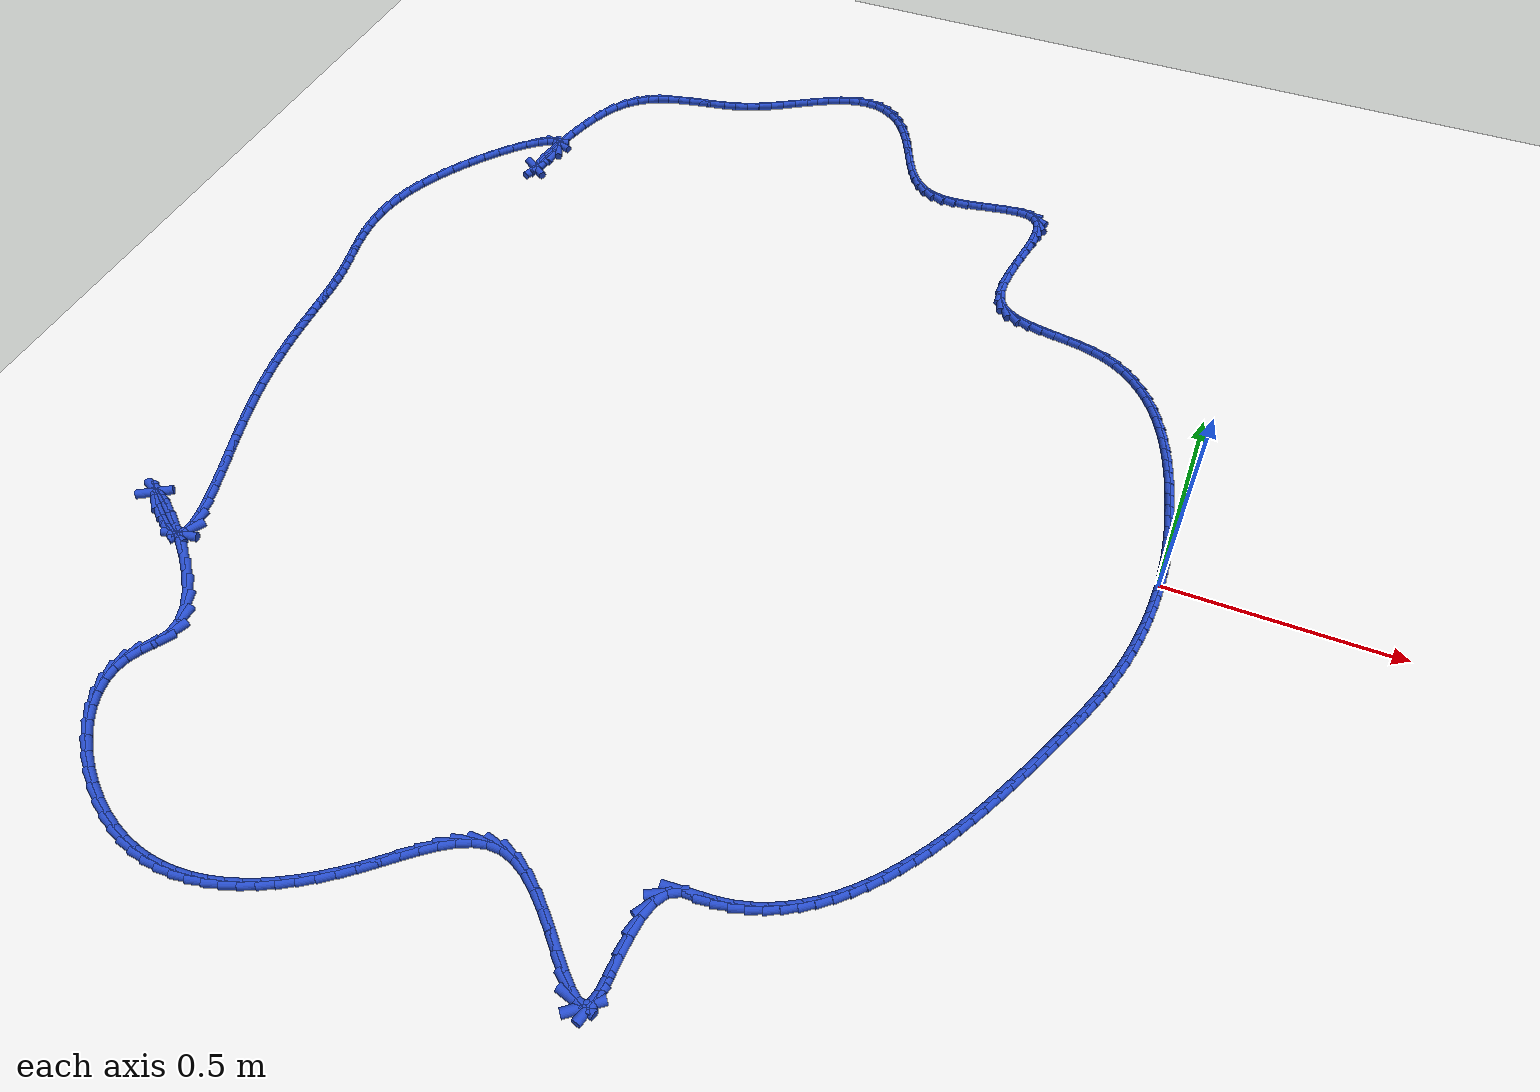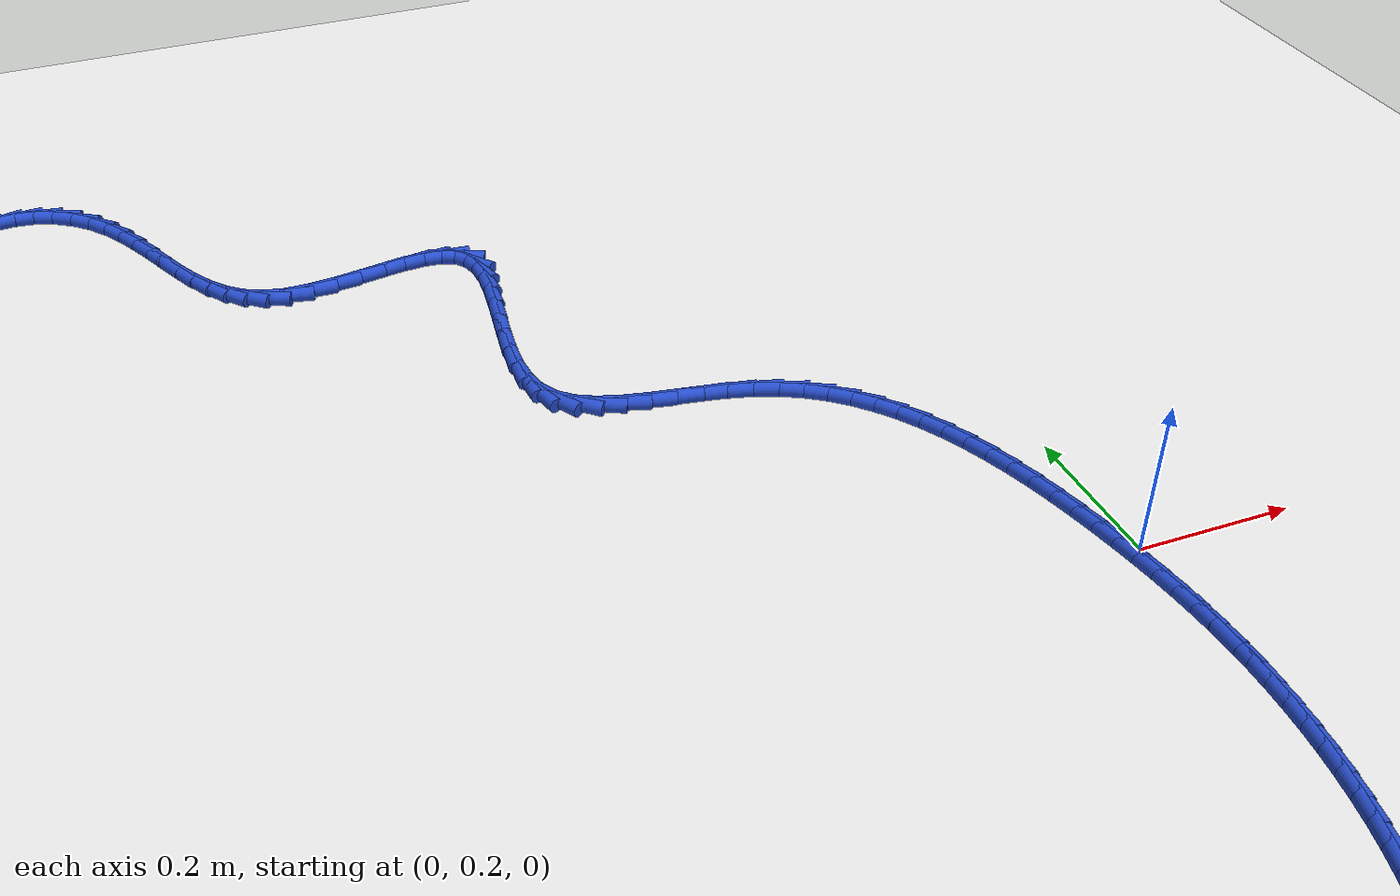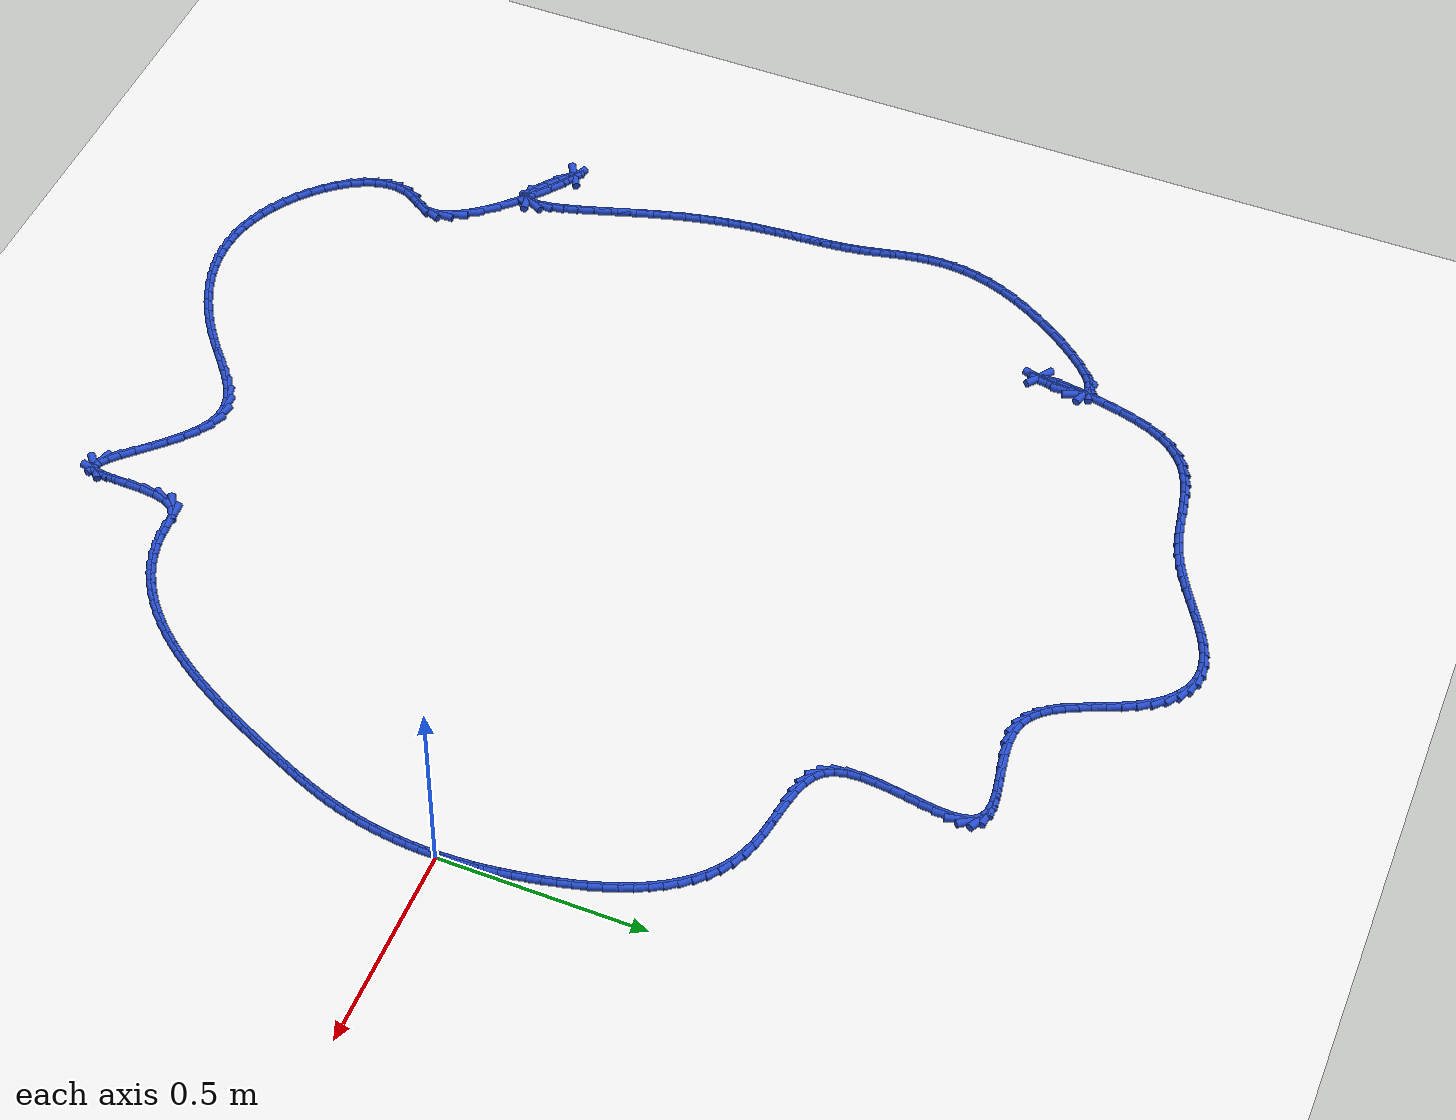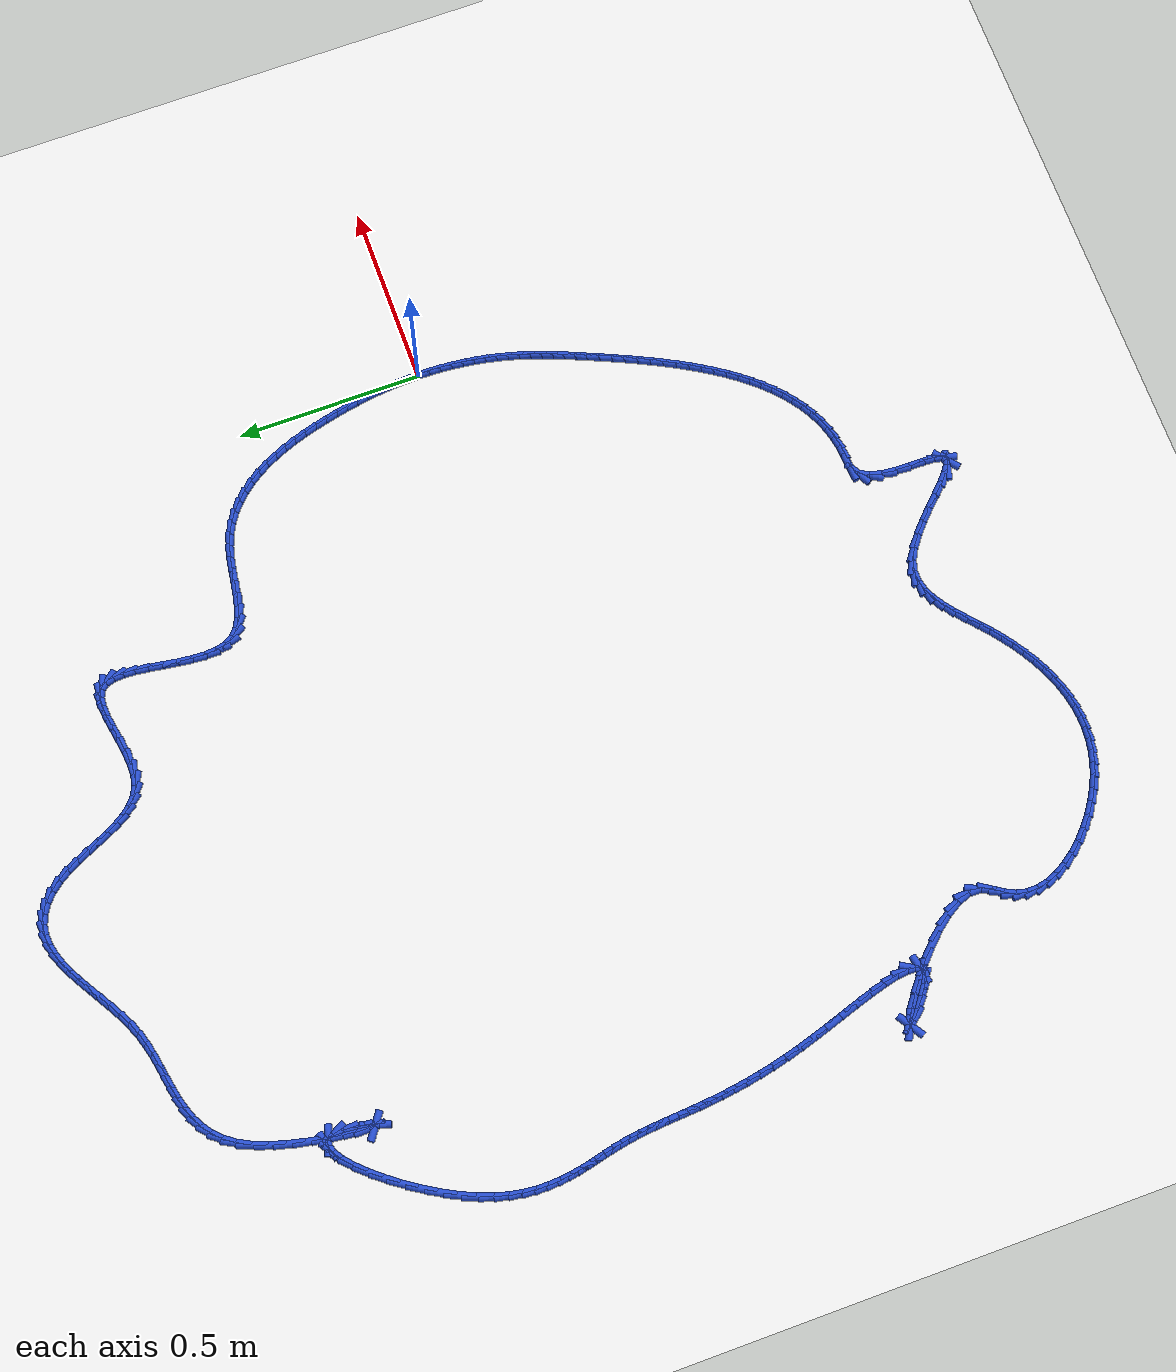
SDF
<sdf version="1.6">
 <world name="default">
  <light name="sun" type="directional">
   <pose>0 0 10 0 -0 0</pose>
   <diffuse>0.8 0.8 0.8 1</diffuse>
   <specular>0.2 0.2 0.2 1</specular>
   <attenuation>
    <range>1000</range>
    <constant>0.9</constant>
    <linear>0.01</linear>
    <quadratic>0.001</quadratic>
   </attenuation>
   <direction>-0.5 0.1 -0.9</direction>
  </light>
  <model name="ground_plane">
   <static>1</static>
   <link name="link">
    <collision name="collision">
     <geometry><plane><normal>0 0 1</normal><size>100 100</size></plane></geometry>
     <surface><friction><ode><mu>100</mu><mu2>50</mu2></ode></friction></surface>
    </collision>
    <visual name="visual">
     <cast_shadows>0</cast_shadows>
     <geometry><plane><normal>0 0 1</normal><size>100 100</size></plane></geometry>
     <material>
      <script><uri>file://media/materials/scripts/gazebo.material</uri><name>Gazebo/WhiteGlow</name></script>
     </material>
    </visual>
   </link>
  </model>
  <gravity>0 0 -9.8</gravity>
  <magnetic_field>6e-06 2.3e-05 -4.2e-05</magnetic_field>
  <atmosphere type="adiabatic"/>
  <physics name="default_physics" default="0" type="ode">
   <max_step_size>0.001</max_step_size>
   <real_time_factor>1</real_time_factor>
   <real_time_update_rate>1000</real_time_update_rate>
  </physics>
  <scene><ambient>0.4 0.4 0.4 1</ambient><background>0.7 0.7 0.7 1</background><shadows>1</shadows></scene>
  <spherical_coordinates>
   <surface_model>EARTH_WGS84</surface_model>
   <latitude_deg>0</latitude_deg>
   <longitude_deg>0</longitude_deg>
   <elevation>0</elevation>
   <heading_deg>0</heading_deg>
  </spherical_coordinates>
  <model name="line">
   <link name="link_0">
    <pose>-9.107298248878237e-18 -2.7755575615628914e-17 0.01 0 1.57 -1.5487160441781933</pose>
    <collision name="collision">
     <geometry><cylinder><radius>0.01</radius><length>0.08</length></cylinder></geometry>
    </collision>
    <visual name="visual">
     <material>
      <script><name>Gazebo/Blue</name><uri>file://media/materials/scripts/gazebo.material</uri></script>
     </material>
     <geometry><cylinder><radius>0.01</radius><length>0.08</length></cylinder></geometry>
    </visual>
   </link>
   <link name="link_1">
    <pose>-0.0006711619609511116 0.030391498901429427 0.01 0 1.57 -1.5174680190827952</pose>
    <collision name="collision">
     <geometry><cylinder><radius>0.01</radius><length>0.08</length></cylinder></geometry>
    </collision>
    <visual name="visual">
     <material>
      <script><name>Gazebo/Blue</name><uri>file://media/materials/scripts/gazebo.material</uri></script>
     </material>
     <geometry><cylinder><radius>0.01</radius><length>0.08</length></cylinder></geometry>
    </visual>
   </link>
   <link name="link_2">
    <pose>-0.0022849066805259036 0.06062337232669993 0.01 0 1.57 -1.4873679906136286</pose>
    <collision name="collision">
     <geometry><cylinder><radius>0.01</radius><length>0.08</length></cylinder></geometry>
    </collision>
    <visual name="visual">
     <material>
      <script><name>Gazebo/Blue</name><uri>file://media/materials/scripts/gazebo.material</uri></script>
     </material>
     <geometry><cylinder><radius>0.01</radius><length>0.08</length></cylinder></geometry>
    </visual>
   </link>
   <link name="link_3">
    <pose>-0.0048081248614214285 0.09079730926587781 0.01 0 1.57 -1.4587643486130544</pose>
    <collision name="collision">
     <geometry><cylinder><radius>0.01</radius><length>0.08</length></cylinder></geometry>
    </collision>
    <visual name="visual">
     <material>
      <script><name>Gazebo/Blue</name><uri>file://media/materials/scripts/gazebo.material</uri></script>
     </material>
     <geometry><cylinder><radius>0.01</radius><length>0.08</length></cylinder></geometry>
    </visual>
   </link>
   <link name="link_4">
    <pose>-0.008207707206334732 0.12101499870902929 0.01 0 1.57 -1.4319588433765889</pose>
    <collision name="collision">
     <geometry><cylinder><radius>0.01</radius><length>0.08</length></cylinder></geometry>
    </collision>
    <visual name="visual">
     <material>
      <script><name>Gazebo/Blue</name><uri>file://media/materials/scripts/gazebo.material</uri></script>
     </material>
     <geometry><cylinder><radius>0.01</radius><length>0.08</length></cylinder></geometry>
    </visual>
   </link>
   <link name="link_5">
    <pose>-0.012450544417962858 0.1513781296462207 0.01 0 1.57 -1.4071968913392146</pose>
    <collision name="collision">
     <geometry><cylinder><radius>0.01</radius><length>0.08</length></cylinder></geometry>
    </collision>
    <visual name="visual">
     <material>
      <script><name>Gazebo/Blue</name><uri>file://media/materials/scripts/gazebo.material</uri></script>
     </material>
     <geometry><cylinder><radius>0.01</radius><length>0.08</length></cylinder></geometry>
    </visual>
   </link>
   <link name="link_6">
    <pose>-0.01750352719900286 0.18198839106751827 0.01 0 1.57 -1.3846624284830191</pose>
    <collision name="collision">
     <geometry><cylinder><radius>0.01</radius><length>0.08</length></cylinder></geometry>
    </collision>
    <visual name="visual">
     <material>
      <script><name>Gazebo/Blue</name><uri>file://media/materials/scripts/gazebo.material</uri></script>
     </material>
     <geometry><cylinder><radius>0.01</radius><length>0.08</length></cylinder></geometry>
    </visual>
   </link>
   <link name="link_7">
    <pose>-0.02333354625215177 0.21294747196298824 0.01 0 1.57 -1.3643820310408041</pose>
    <collision name="collision">
     <geometry><cylinder><radius>0.01</radius><length>0.08</length></cylinder></geometry>
    </collision>
    <visual name="visual">
     <material>
      <script><name>Gazebo/Blue</name><uri>file://media/materials/scripts/gazebo.material</uri></script>
     </material>
     <geometry><cylinder><radius>0.01</radius><length>0.08</length></cylinder></geometry>
    </visual>
   </link>
   <link name="link_8">
    <pose>-0.02990960083578653 0.24435224060416774 0.01 0 1.57 -1.34336765029454</pose>
    <collision name="collision">
     <geometry><cylinder><radius>0.01</radius><length>0.08</length></cylinder></geometry>
    </collision>
    <visual name="visual">
     <material>
      <script><name>Gazebo/Blue</name><uri>file://media/materials/scripts/gazebo.material</uri></script>
     </material>
     <geometry><cylinder><radius>0.01</radius><length>0.08</length></cylinder></geometry>
    </visual>
   </link>
   <link name="link_9">
    <pose>-0.03726776562247872 0.27614621304375275 0.01 0 1.57 -1.317895623288179</pose>
    <collision name="collision">
     <geometry><cylinder><radius>0.01</radius><length>0.08</length></cylinder></geometry>
    </collision>
    <visual name="visual">
     <material>
      <script><name>Gazebo/Blue</name><uri>file://media/materials/scripts/gazebo.material</uri></script>
     </material>
     <geometry><cylinder><radius>0.01</radius><length>0.08</length></cylinder></geometry>
    </visual>
   </link>
   <link name="link_10">
    <pose>-0.04552349521653706 0.30809142171917586 0.01 0 1.57 -1.2874552609864258</pose>
    <collision name="collision">
     <geometry><cylinder><radius>0.01</radius><length>0.08</length></cylinder></geometry>
    </collision>
    <visual name="visual">
     <material>
      <script><name>Gazebo/Blue</name><uri>file://media/materials/scripts/gazebo.material</uri></script>
     </material>
     <geometry><cylinder><radius>0.01</radius><length>0.08</length></cylinder></geometry>
    </visual>
   </link>
   <link name="link_11">
    <pose>-0.054796835586308545 0.339939401989749 0.01 0 1.57 -1.251612497408351</pose>
    <collision name="collision">
     <geometry><cylinder><radius>0.01</radius><length>0.08</length></cylinder></geometry>
    </collision>
    <visual name="visual">
     <material>
      <script><name>Gazebo/Blue</name><uri>file://media/materials/scripts/gazebo.material</uri></script>
     </material>
     <geometry><cylinder><radius>0.01</radius><length>0.08</length></cylinder></geometry>
    </visual>
   </link>
   <link name="link_12">
    <pose>-0.06520783270014013 0.37144168921478404 0.01 0 1.57 -1.209810733027695</pose>
    <collision name="collision">
     <geometry><cylinder><radius>0.01</radius><length>0.08</length></cylinder></geometry>
    </collision>
    <visual name="visual">
     <material>
      <script><name>Gazebo/Blue</name><uri>file://media/materials/scripts/gazebo.material</uri></script>
     </material>
     <geometry><cylinder><radius>0.01</radius><length>0.08</length></cylinder></geometry>
    </visual>
   </link>
   <link name="link_13">
    <pose>-0.07687653252637883 0.4023498187535929 0.01 0 1.57 -1.1613828268277069</pose>
    <collision name="collision">
     <geometry><cylinder><radius>0.01</radius><length>0.08</length></cylinder></geometry>
    </collision>
    <visual name="visual">
     <material>
      <script><name>Gazebo/Blue</name><uri>file://media/materials/scripts/gazebo.material</uri></script>
     </material>
     <geometry><cylinder><radius>0.01</radius><length>0.08</length></cylinder></geometry>
    </visual>
   </link>
   <link name="link_14">
    <pose>-0.08992298103337162 0.4324153259654876 0.01 0 1.57 -1.1055752439118254</pose>
    <collision name="collision">
     <geometry><cylinder><radius>0.01</radius><length>0.08</length></cylinder></geometry>
    </collision>
    <visual name="visual">
     <material>
      <script><name>Gazebo/Blue</name><uri>file://media/materials/scripts/gazebo.material</uri></script>
     </material>
     <geometry><cylinder><radius>0.01</radius><length>0.08</length></cylinder></geometry>
    </visual>
   </link>
   <link name="link_15">
    <pose>-0.10446722418946548 0.46138974620977985 0.01 0 1.57 -1.0415955799346688</pose>
    <collision name="collision">
     <geometry><cylinder><radius>0.01</radius><length>0.08</length></cylinder></geometry>
    </collision>
    <visual name="visual">
     <material>
      <script><name>Gazebo/Blue</name><uri>file://media/materials/scripts/gazebo.material</uri></script>
     </material>
     <geometry><cylinder><radius>0.01</radius><length>0.08</length></cylinder></geometry>
    </visual>
   </link>
   <link name="link_16">
    <pose>-0.12062930796300736 0.4890246148457817 0.01 0 1.57 -0.9686977700942155</pose>
    <collision name="collision">
     <geometry><cylinder><radius>0.01</radius><length>0.08</length></cylinder></geometry>
    </collision>
    <visual name="visual">
     <material>
      <script><name>Gazebo/Blue</name><uri>file://media/materials/scripts/gazebo.material</uri></script>
     </material>
     <geometry><cylinder><radius>0.01</radius><length>0.08</length></cylinder></geometry>
    </visual>
   </link>
   <link name="link_17">
    <pose>-0.13852927832234432 0.515071467232805 0.01 0 1.57 -0.8863196126066907</pose>
    <collision name="collision">
     <geometry><cylinder><radius>0.01</radius><length>0.08</length></cylinder></geometry>
    </collision>
    <visual name="visual">
     <material>
      <script><name>Gazebo/Blue</name><uri>file://media/materials/scripts/gazebo.material</uri></script>
     </material>
     <geometry><cylinder><radius>0.01</radius><length>0.08</length></cylinder></geometry>
    </visual>
   </link>
   <link name="link_18">
    <pose>-0.15828718123582322 0.5392818387301614 0.01 0 1.57 -0.7942792094157315</pose>
    <collision name="collision">
     <geometry><cylinder><radius>0.01</radius><length>0.08</length></cylinder></geometry>
    </collision>
    <visual name="visual">
     <material>
      <script><name>Gazebo/Blue</name><uri>file://media/materials/scripts/gazebo.material</uri></script>
     </material>
     <geometry><cylinder><radius>0.01</radius><length>0.08</length></cylinder></geometry>
    </visual>
   </link>
   <link name="link_19">
    <pose>-0.18002306267179125 0.5614072646971636 0.01 0 1.57 -0.6930130803756717</pose>
    <collision name="collision">
     <geometry><cylinder><radius>0.01</radius><length>0.08</length></cylinder></geometry>
    </collision>
    <visual name="visual">
     <material>
      <script><name>Gazebo/Blue</name><uri>file://media/materials/scripts/gazebo.material</uri></script>
     </material>
     <geometry><cylinder><radius>0.01</radius><length>0.08</length></cylinder></geometry>
    </visual>
   </link>
   <link name="link_20">
    <pose>-0.20385696859859517 0.5811992804931227 0.01 0 1.57 -0.5837963238916771</pose>
    <collision name="collision">
     <geometry><cylinder><radius>0.01</radius><length>0.08</length></cylinder></geometry>
    </collision>
    <visual name="visual">
     <material>
      <script><name>Gazebo/Blue</name><uri>file://media/materials/scripts/gazebo.material</uri></script>
     </material>
     <geometry><cylinder><radius>0.01</radius><length>0.08</length></cylinder></geometry>
    </visual>
   </link>
   <link name="link_21">
    <pose>-0.22990894498458214 0.598409421477351 0.01 0 1.57 -0.4688402312000771</pose>
    <collision name="collision">
     <geometry><cylinder><radius>0.01</radius><length>0.08</length></cylinder></geometry>
    </collision>
    <visual name="visual">
     <material>
      <script><name>Gazebo/Blue</name><uri>file://media/materials/scripts/gazebo.material</uri></script>
     </material>
     <geometry><cylinder><radius>0.01</radius><length>0.08</length></cylinder></geometry>
    </visual>
   </link>
   <link name="link_22">
    <pose>-0.2582990377980991 0.6127892230091604 0.01 0 1.57 -0.35122392846613315</pose>
    <collision name="collision">
     <geometry><cylinder><radius>0.01</radius><length>0.08</length></cylinder></geometry>
    </collision>
    <visual name="visual">
     <material>
      <script><name>Gazebo/Blue</name><uri>file://media/materials/scripts/gazebo.material</uri></script>
     </material>
     <geometry><cylinder><radius>0.01</radius><length>0.08</length></cylinder></geometry>
    </visual>
   </link>
   <link name="link_23">
    <pose>-0.28914573059034954 0.6240919487211962 0.01 0 1.57 -0.24725509992650535</pose>
    <collision name="collision">
     <geometry><cylinder><radius>0.01</radius><length>0.08</length></cylinder></geometry>
    </collision>
    <visual name="visual">
     <material>
      <script><name>Gazebo/Blue</name><uri>file://media/materials/scripts/gazebo.material</uri></script>
     </material>
     <geometry><cylinder><radius>0.01</radius><length>0.08</length></cylinder></geometry>
    </visual>
   </link>
   <link name="link_24">
    <pose>-0.32223081965496275 0.6324432900651165 0.01 0 1.57 -0.18306010486583105</pose>
    <collision name="collision">
     <geometry><cylinder><radius>0.01</radius><length>0.08</length></cylinder></geometry>
    </collision>
    <visual name="visual">
     <material>
      <script><name>Gazebo/Blue</name><uri>file://media/materials/scripts/gazebo.material</uri></script>
     </material>
     <geometry><cylinder><radius>0.01</radius><length>0.08</length></cylinder></geometry>
    </visual>
   </link>
   <link name="link_25">
    <pose>-0.35658221090065695 0.6388028570490718 0.01 0 1.57 -0.15622098834988132</pose>
    <collision name="collision">
     <geometry><cylinder><radius>0.01</radius><length>0.08</length></cylinder></geometry>
    </collision>
    <visual name="visual">
     <material>
      <script><name>Gazebo/Blue</name><uri>file://media/materials/scripts/gazebo.material</uri></script>
     </material>
     <geometry><cylinder><radius>0.01</radius><length>0.08</length></cylinder></geometry>
    </visual>
   </link>
   <link name="link_26">
    <pose>-0.3911253846828628 0.6442435580747926 0.01 0 1.57 -0.16470554279743305</pose>
    <collision name="collision">
     <geometry><cylinder><radius>0.01</radius><length>0.08</length></cylinder></geometry>
    </collision>
    <visual name="visual">
     <material>
      <script><name>Gazebo/Blue</name><uri>file://media/materials/scripts/gazebo.material</uri></script>
     </material>
     <geometry><cylinder><radius>0.01</radius><length>0.08</length></cylinder></geometry>
    </visual>
   </link>
   <link name="link_27">
    <pose>-0.4247858213570115 0.6498383015440096 0.01 0 1.57 -0.21194229378995613</pose>
    <collision name="collision">
     <geometry><cylinder><radius>0.01</radius><length>0.08</length></cylinder></geometry>
    </collision>
    <visual name="visual">
     <material>
      <script><name>Gazebo/Blue</name><uri>file://media/materials/scripts/gazebo.material</uri></script>
     </material>
     <geometry><cylinder><radius>0.01</radius><length>0.08</length></cylinder></geometry>
    </visual>
   </link>
   <link name="link_28">
    <pose>-0.4564890012785339 0.6566599958584531 0.01 0 1.57 -0.3080158597506141</pose>
    <collision name="collision">
     <geometry><cylinder><radius>0.01</radius><length>0.08</length></cylinder></geometry>
    </collision>
    <visual name="visual">
     <material>
      <script><name>Gazebo/Blue</name><uri>file://media/materials/scripts/gazebo.material</uri></script>
     </material>
     <geometry><cylinder><radius>0.01</radius><length>0.08</length></cylinder></geometry>
    </visual>
   </link>
   <link name="link_29">
    <pose>-0.4851604048028605 0.6657815494198535 0.01 0 1.57 -0.4705203304105009</pose>
    <collision name="collision">
     <geometry><cylinder><radius>0.01</radius><length>0.08</length></cylinder></geometry>
    </collision>
    <visual name="visual">
     <material>
      <script><name>Gazebo/Blue</name><uri>file://media/materials/scripts/gazebo.material</uri></script>
     </material>
     <geometry><cylinder><radius>0.01</radius><length>0.08</length></cylinder></geometry>
    </visual>
   </link>
   <link name="link_30">
    <pose>-0.5097255122854228 0.6782758706299414 0.01 0 1.57 -0.7182085423369431</pose>
    <collision name="collision">
     <geometry><cylinder><radius>0.01</radius><length>0.08</length></cylinder></geometry>
    </collision>
    <visual name="visual">
     <material>
      <script><name>Gazebo/Blue</name><uri>file://media/materials/scripts/gazebo.material</uri></script>
     </material>
     <geometry><cylinder><radius>0.01</radius><length>0.08</length></cylinder></geometry>
    </visual>
   </link>
   <link name="link_31">
    <pose>-0.5291098040816513 0.695215867890447 0.01 0 1.57 -1.039429248445565</pose>
    <collision name="collision">
     <geometry><cylinder><radius>0.01</radius><length>0.08</length></cylinder></geometry>
    </collision>
    <visual name="visual">
     <material>
      <script><name>Gazebo/Blue</name><uri>file://media/materials/scripts/gazebo.material</uri></script>
     </material>
     <geometry><cylinder><radius>0.01</radius><length>0.08</length></cylinder></geometry>
    </visual>
   </link>
   <link name="link_32">
    <pose>-0.5422837329436971 0.717629852527886 0.01 0 1.57 -1.3236414079525096</pose>
    <collision name="collision">
     <geometry><cylinder><radius>0.01</radius><length>0.08</length></cylinder></geometry>
    </collision>
    <visual name="visual">
     <material>
      <script><name>Gazebo/Blue</name><uri>file://media/materials/scripts/gazebo.material</uri></script>
     </material>
     <geometry><cylinder><radius>0.01</radius><length>0.08</length></cylinder></geometry>
    </visual>
   </link>
   <link name="link_33">
    <pose>-0.5493071312710457 0.7454658477451037 0.01 0 1.57 -1.5068990331410062</pose>
    <collision name="collision">
     <geometry><cylinder><radius>0.01</radius><length>0.08</length></cylinder></geometry>
    </collision>
    <visual name="visual">
     <material>
      <script><name>Gazebo/Blue</name><uri>file://media/materials/scripts/gazebo.material</uri></script>
     </material>
     <geometry><cylinder><radius>0.01</radius><length>0.08</length></cylinder></geometry>
    </visual>
   </link>
   <link name="link_34">
    <pose>-0.5513606806796135 0.7775603816845239 0.01 0 1.57 1.5228987435027548</pose>
    <collision name="collision">
     <geometry><cylinder><radius>0.01</radius><length>0.08</length></cylinder></geometry>
    </collision>
    <visual name="visual">
     <material>
      <script><name>Gazebo/Blue</name><uri>file://media/materials/scripts/gazebo.material</uri></script>
     </material>
     <geometry><cylinder><radius>0.01</radius><length>0.08</length></cylinder></geometry>
    </visual>
   </link>
   <link name="link_35">
    <pose>-0.5496763306960403 0.8126991424391762 0.01 0 1.57 1.4579307255046015</pose>
    <collision name="collision">
     <geometry><cylinder><radius>0.01</radius><length>0.08</length></cylinder></geometry>
    </collision>
    <visual name="visual">
     <material>
      <script><name>Gazebo/Blue</name><uri>file://media/materials/scripts/gazebo.material</uri></script>
     </material>
     <geometry><cylinder><radius>0.01</radius><length>0.08</length></cylinder></geometry>
    </visual>
   </link>
   <link name="link_36">
    <pose>-0.5454860308469653 0.8496678181020901 0.01 0 1.57 1.4264199918031013</pose>
    <collision name="collision">
     <geometry><cylinder><radius>0.01</radius><length>0.08</length></cylinder></geometry>
    </collision>
    <visual name="visual">
     <material>
      <script><name>Gazebo/Blue</name><uri>file://media/materials/scripts/gazebo.material</uri></script>
     </material>
     <geometry><cylinder><radius>0.01</radius><length>0.08</length></cylinder></geometry>
    </visual>
   </link>
   <link name="link_37">
    <pose>-0.5400217306590289 0.8872520967662952 0.01 0 1.57 1.4230035168919142</pose>
    <collision name="collision">
     <geometry><cylinder><radius>0.01</radius><length>0.08</length></cylinder></geometry>
    </collision>
    <visual name="visual">
     <material>
      <script><name>Gazebo/Blue</name><uri>file://media/materials/scripts/gazebo.material</uri></script>
     </material>
     <geometry><cylinder><radius>0.01</radius><length>0.08</length></cylinder></geometry>
    </visual>
   </link>
   <link name="link_38">
    <pose>-0.5345153796588704 0.9242376665248203 0.01 0 1.57 1.4486847227458415</pose>
    <collision name="collision">
     <geometry><cylinder><radius>0.01</radius><length>0.08</length></cylinder></geometry>
    </collision>
    <visual name="visual">
     <material>
      <script><name>Gazebo/Blue</name><uri>file://media/materials/scripts/gazebo.material</uri></script>
     </material>
     <geometry><cylinder><radius>0.01</radius><length>0.08</length></cylinder></geometry>
    </visual>
   </link>
   <link name="link_39">
    <pose>-0.5301989273731297 0.9594102154706959 0.01 0 1.57 1.5119255209368108</pose>
    <collision name="collision">
     <geometry><cylinder><radius>0.01</radius><length>0.08</length></cylinder></geometry>
    </collision>
    <visual name="visual">
     <material>
      <script><name>Gazebo/Blue</name><uri>file://media/materials/scripts/gazebo.material</uri></script>
     </material>
     <geometry><cylinder><radius>0.01</radius><length>0.08</length></cylinder></geometry>
    </visual>
   </link>
   <link name="link_40">
    <pose>-0.5283043233284467 0.9915554316969507 0.01 0 1.57 -1.5078341900095376</pose>
    <collision name="collision">
     <geometry><cylinder><radius>0.01</radius><length>0.08</length></cylinder></geometry>
    </collision>
    <visual name="visual">
     <material>
      <script><name>Gazebo/Blue</name><uri>file://media/materials/scripts/gazebo.material</uri></script>
     </material>
     <geometry><cylinder><radius>0.01</radius><length>0.08</length></cylinder></geometry>
    </visual>
   </link>
   <link name="link_41">
    <pose>-0.5300635170514608 1.0194590032966147 0.01 0 1.57 -1.2829949780270735</pose>
    <collision name="collision">
     <geometry><cylinder><radius>0.01</radius><length>0.08</length></cylinder></geometry>
    </collision>
    <visual name="visual">
     <material>
      <script><name>Gazebo/Blue</name><uri>file://media/materials/scripts/gazebo.material</uri></script>
     </material>
     <geometry><cylinder><radius>0.01</radius><length>0.08</length></cylinder></geometry>
    </visual>
   </link>
   <link name="link_42">
    <pose>-0.5367084580688121 1.041906618362717 0.01 0 1.57 -0.8906405508435817</pose>
    <collision name="collision">
     <geometry><cylinder><radius>0.01</radius><length>0.08</length></cylinder></geometry>
    </collision>
    <visual name="visual">
     <material>
      <script><name>Gazebo/Blue</name><uri>file://media/materials/scripts/gazebo.material</uri></script>
     </material>
     <geometry><cylinder><radius>0.01</radius><length>0.08</length></cylinder></geometry>
    </visual>
   </link>
   <link name="link_43">
    <pose>-0.5494710740412702 1.0576839893649224 0.01 0 1.57 -0.40551260671328465</pose>
    <collision name="collision">
     <geometry><cylinder><radius>0.01</radius><length>0.08</length></cylinder></geometry>
    </collision>
    <visual name="visual">
     <material>
      <script><name>Gazebo/Blue</name><uri>file://media/materials/scripts/gazebo.material</uri></script>
     </material>
     <geometry><cylinder><radius>0.01</radius><length>0.08</length></cylinder></geometry>
    </visual>
   </link>
   <link name="link_44">
    <pose>-0.5691031095274153 1.0661121492754488 0.01 0 1.57 -0.0904721181696937</pose>
    <collision name="collision">
     <geometry><cylinder><radius>0.01</radius><length>0.08</length></cylinder></geometry>
    </collision>
    <visual name="visual">
     <material>
      <script><name>Gazebo/Blue</name><uri>file://media/materials/scripts/gazebo.material</uri></script>
     </material>
     <geometry><cylinder><radius>0.01</radius><length>0.08</length></cylinder></geometry>
    </visual>
   </link>
   <link name="link_45">
    <pose>-0.5946372348585163 1.0684285993368305 0.01 0 1.57 0.07065173461353581</pose>
    <collision name="collision">
     <geometry><cylinder><radius>0.01</radius><length>0.08</length></cylinder></geometry>
    </collision>
    <visual name="visual">
     <material>
      <script><name>Gazebo/Blue</name><uri>file://media/materials/scripts/gazebo.material</uri></script>
     </material>
     <geometry><cylinder><radius>0.01</radius><length>0.08</length></cylinder></geometry>
    </visual>
   </link>
   <link name="link_46">
    <pose>-0.6247215721735363 1.0662995450309274 0.01 0 1.57 0.1464193417690288</pose>
    <collision name="collision">
     <geometry><cylinder><radius>0.01</radius><length>0.08</length></cylinder></geometry>
    </collision>
    <visual name="visual">
     <material>
      <script><name>Gazebo/Blue</name><uri>file://media/materials/scripts/gazebo.material</uri></script>
     </material>
     <geometry><cylinder><radius>0.01</radius><length>0.08</length></cylinder></geometry>
    </visual>
   </link>
   <link name="link_47">
    <pose>-0.6580042436114384 1.061391191839598 0.01 0 1.57 0.16975920438952974</pose>
    <collision name="collision">
     <geometry><cylinder><radius>0.01</radius><length>0.08</length></cylinder></geometry>
    </collision>
    <visual name="visual">
     <material>
      <script><name>Gazebo/Blue</name><uri>file://media/materials/scripts/gazebo.material</uri></script>
     </material>
     <geometry><cylinder><radius>0.01</radius><length>0.08</length></cylinder></geometry>
    </visual>
   </link>
   <link name="link_48">
    <pose>-0.693133371311186 1.055369745244702 0.01 0 1.57 0.15231378318291702</pose>
    <collision name="collision">
     <geometry><cylinder><radius>0.01</radius><length>0.08</length></cylinder></geometry>
    </collision>
    <visual name="visual">
     <material>
      <script><name>Gazebo/Blue</name><uri>file://media/materials/scripts/gazebo.material</uri></script>
     </material>
     <geometry><cylinder><radius>0.01</radius><length>0.08</length></cylinder></geometry>
    </visual>
   </link>
   <link name="link_49">
    <pose>-0.728757077411742 1.0499014107280986 0.01 0 1.57 0.09318213129982199</pose>
    <collision name="collision">
     <geometry><cylinder><radius>0.01</radius><length>0.08</length></cylinder></geometry>
    </collision>
    <visual name="visual">
     <material>
      <script><name>Gazebo/Blue</name><uri>file://media/materials/scripts/gazebo.material</uri></script>
     </material>
     <geometry><cylinder><radius>0.01</radius><length>0.08</length></cylinder></geometry>
    </visual>
   </link>
   <link name="link_50">
    <pose>-0.7635234840520695 1.0466523937716472 0.01 0 1.57 -0.019547886074322254</pose>
    <collision name="collision">
     <geometry><cylinder><radius>0.01</radius><length>0.08</length></cylinder></geometry>
    </collision>
    <visual name="visual">
     <material>
      <script><name>Gazebo/Blue</name><uri>file://media/materials/scripts/gazebo.material</uri></script>
     </material>
     <geometry><cylinder><radius>0.01</radius><length>0.08</length></cylinder></geometry>
    </visual>
   </link>
   <link name="link_51">
    <pose>-0.7960807133711314 1.0472888998572072 0.01 0 1.57 -0.2095122326451276</pose>
    <collision name="collision">
     <geometry><cylinder><radius>0.01</radius><length>0.08</length></cylinder></geometry>
    </collision>
    <visual name="visual">
     <material>
      <script><name>Gazebo/Blue</name><uri>file://media/materials/scripts/gazebo.material</uri></script>
     </material>
     <geometry><cylinder><radius>0.01</radius><length>0.08</length></cylinder></geometry>
    </visual>
   </link>
   <link name="link_52">
    <pose>-0.8250921631158185 1.0534576790010977 0.01 0 1.57 -0.4603297266119786</pose>
    <collision name="collision">
     <geometry><cylinder><radius>0.01</radius><length>0.08</length></cylinder></geometry>
    </collision>
    <visual name="visual">
     <material>
      <script><name>Gazebo/Blue</name><uri>file://media/materials/scripts/gazebo.material</uri></script>
     </material>
     <geometry><cylinder><radius>0.01</radius><length>0.08</length></cylinder></geometry>
    </visual>
   </link>
   <link name="link_53">
    <pose>-0.8500029112896328 1.0658099101517697 0.01 0 1.57 -0.6921397278806337</pose>
    <collision name="collision">
     <geometry><cylinder><radius>0.01</radius><length>0.08</length></cylinder></geometry>
    </collision>
    <visual name="visual">
     <material>
      <script><name>Gazebo/Blue</name><uri>file://media/materials/scripts/gazebo.material</uri></script>
     </material>
     <geometry><cylinder><radius>0.01</radius><length>0.08</length></cylinder></geometry>
    </visual>
   </link>
   <link name="link_54">
    <pose>-0.8713978719821538 1.0835450433444678 0.01 0 1.57 -0.8746788705650897</pose>
    <collision name="collision">
     <geometry><cylinder><radius>0.01</radius><length>0.08</length></cylinder></geometry>
    </collision>
    <visual name="visual">
     <material>
      <script><name>Gazebo/Blue</name><uri>file://media/materials/scripts/gazebo.material</uri></script>
     </material>
     <geometry><cylinder><radius>0.01</radius><length>0.08</length></cylinder></geometry>
    </visual>
   </link>
   <link name="link_55">
    <pose>-0.88995207624401 1.105747752990534 0.01 0 1.57 -1.0040958911483306</pose>
    <collision name="collision">
     <geometry><cylinder><radius>0.01</radius><length>0.08</length></cylinder></geometry>
    </collision>
    <visual name="visual">
     <material>
      <script><name>Gazebo/Blue</name><uri>file://media/materials/scripts/gazebo.material</uri></script>
     </material>
     <geometry><cylinder><radius>0.01</radius><length>0.08</length></cylinder></geometry>
    </visual>
   </link>
   <link name="link_56">
    <pose>-0.9063405551258295 1.131502713501311 0.01 0 1.57 -1.0875690097782078</pose>
    <collision name="collision">
     <geometry><cylinder><radius>0.01</radius><length>0.08</length></cylinder></geometry>
    </collision>
    <visual name="visual">
     <material>
      <script><name>Gazebo/Blue</name><uri>file://media/materials/scripts/gazebo.material</uri></script>
     </material>
     <geometry><cylinder><radius>0.01</radius><length>0.08</length></cylinder></geometry>
    </visual>
   </link>
   <link name="link_57">
    <pose>-0.9212383396782402 1.1598945992881395 0.01 0 1.57 -1.1333742571657481</pose>
    <collision name="collision">
     <geometry><cylinder><radius>0.01</radius><length>0.08</length></cylinder></geometry>
    </collision>
    <visual name="visual">
     <material>
      <script><name>Gazebo/Blue</name><uri>file://media/materials/scripts/gazebo.material</uri></script>
     </material>
     <geometry><cylinder><radius>0.01</radius><length>0.08</length></cylinder></geometry>
    </visual>
   </link>
   <link name="link_58">
    <pose>-0.935320460951871 1.190008084762364 0.01 0 1.57 -1.1472004085185488</pose>
    <collision name="collision">
     <geometry><cylinder><radius>0.01</radius><length>0.08</length></cylinder></geometry>
    </collision>
    <visual name="visual">
     <material>
      <script><name>Gazebo/Blue</name><uri>file://media/materials/scripts/gazebo.material</uri></script>
     </material>
     <geometry><cylinder><radius>0.01</radius><length>0.08</length></cylinder></geometry>
    </visual>
   </link>
   <link name="link_59">
    <pose>-0.9492619499973498 1.2209278443353249 0.01 0 1.57 -1.131572220488044</pose>
    <collision name="collision">
     <geometry><cylinder><radius>0.01</radius><length>0.08</length></cylinder></geometry>
    </collision>
    <visual name="visual">
     <material>
      <script><name>Gazebo/Blue</name><uri>file://media/materials/scripts/gazebo.material</uri></script>
     </material>
     <geometry><cylinder><radius>0.01</radius><length>0.08</length></cylinder></geometry>
    </visual>
   </link>
   <link name="link_60">
    <pose>-0.9637378378653049 1.2517385524183648 0.01 0 1.57 -1.0861001790822522</pose>
    <collision name="collision">
     <geometry><cylinder><radius>0.01</radius><length>0.08</length></cylinder></geometry>
    </collision>
    <visual name="visual">
     <material>
      <script><name>Gazebo/Blue</name><uri>file://media/materials/scripts/gazebo.material</uri></script>
     </material>
     <geometry><cylinder><radius>0.01</radius><length>0.08</length></cylinder></geometry>
    </visual>
   </link>
   <link name="link_61">
    <pose>-0.9794231556063638 1.2815248834228259 0.01 0 1.57 -1.007931119352681</pose>
    <collision name="collision">
     <geometry><cylinder><radius>0.01</radius><length>0.08</length></cylinder></geometry>
    </collision>
    <visual name="visual">
     <material>
      <script><name>Gazebo/Blue</name><uri>file://media/materials/scripts/gazebo.material</uri></script>
     </material>
     <geometry><cylinder><radius>0.01</radius><length>0.08</length></cylinder></geometry>
    </visual>
   </link>
   <link name="link_62">
    <pose>-0.9969929342711554 1.3093715117600508 0.01 0 1.57 -0.8927462223182837</pose>
    <collision name="collision">
     <geometry><cylinder><radius>0.01</radius><length>0.08</length></cylinder></geometry>
    </collision>
    <visual name="visual">
     <material>
      <script><name>Gazebo/Blue</name><uri>file://media/materials/scripts/gazebo.material</uri></script>
     </material>
     <geometry><cylinder><radius>0.01</radius><length>0.08</length></cylinder></geometry>
    </visual>
   </link>
   <link name="link_63">
    <pose>-1.0171222049103081 1.3343631118413812 0.01 0 1.57 -0.7378774572413543</pose>
    <collision name="collision">
     <geometry><cylinder><radius>0.01</radius><length>0.08</length></cylinder></geometry>
    </collision>
    <visual name="visual">
     <material>
      <script><name>Gazebo/Blue</name><uri>file://media/materials/scripts/gazebo.material</uri></script>
     </material>
     <geometry><cylinder><radius>0.01</radius><length>0.08</length></cylinder></geometry>
    </visual>
   </link>
   <link name="link_64">
    <pose>-1.0404522595737244 1.3555749114047513 0.01 0 1.57 -0.5570568199839954</pose>
    <collision name="collision">
     <geometry><cylinder><radius>0.01</radius><length>0.08</length></cylinder></geometry>
    </collision>
    <visual name="visual">
     <material>
      <script><name>Gazebo/Blue</name><uri>file://media/materials/scripts/gazebo.material</uri></script>
     </material>
     <geometry><cylinder><radius>0.01</radius><length>0.08</length></cylinder></geometry>
    </visual>
   </link>
   <link name="link_65">
    <pose>-1.066407798631495 1.3717415014168965 0.01 0 1.57 -0.3492907592304946</pose>
    <collision name="collision">
     <geometry><cylinder><radius>0.01</radius><length>0.08</length></cylinder></geometry>
    </collision>
    <visual name="visual">
     <material>
      <script><name>Gazebo/Blue</name><uri>file://media/materials/scripts/gazebo.material</uri></script>
     </material>
     <geometry><cylinder><radius>0.01</radius><length>0.08</length></cylinder></geometry>
    </visual>
   </link>
   <link name="link_66">
    <pose>-1.0931664770123652 1.3814876799423863 0.01 0 1.57 -0.13106832094035797</pose>
    <collision name="collision">
     <geometry><cylinder><radius>0.01</radius><length>0.08</length></cylinder></geometry>
    </collision>
    <visual name="visual">
     <material>
      <script><name>Gazebo/Blue</name><uri>file://media/materials/scripts/gazebo.material</uri></script>
     </material>
     <geometry><cylinder><radius>0.01</radius><length>0.08</length></cylinder></geometry>
    </visual>
   </link>
   <link name="link_67">
    <pose>-1.120263568295055 1.3850597282895514 0.01 0 1.57 0.06633668072293741</pose>
    <collision name="collision">
     <geometry><cylinder><radius>0.01</radius><length>0.08</length></cylinder></geometry>
    </collision>
    <visual name="visual">
     <material>
      <script><name>Gazebo/Blue</name><uri>file://media/materials/scripts/gazebo.material</uri></script>
     </material>
     <geometry><cylinder><radius>0.01</radius><length>0.08</length></cylinder></geometry>
    </visual>
   </link>
   <link name="link_68">
    <pose>-1.1477044189930705 1.383236718468083 0.01 0 1.57 0.22767355937240513</pose>
    <collision name="collision">
     <geometry><cylinder><radius>0.01</radius><length>0.08</length></cylinder></geometry>
    </collision>
    <visual name="visual">
     <material>
      <script><name>Gazebo/Blue</name><uri>file://media/materials/scripts/gazebo.material</uri></script>
     </material>
     <geometry><cylinder><radius>0.01</radius><length>0.08</length></cylinder></geometry>
    </visual>
   </link>
   <link name="link_69">
    <pose>-1.17549461089899 1.3767979891579962 0.01 0 1.57 0.350042049003715</pose>
    <collision name="collision">
     <geometry><cylinder><radius>0.01</radius><length>0.08</length></cylinder></geometry>
    </collision>
    <visual name="visual">
     <material>
      <script><name>Gazebo/Blue</name><uri>file://media/materials/scripts/gazebo.material</uri></script>
     </material>
     <geometry><cylinder><radius>0.01</radius><length>0.08</length></cylinder></geometry>
    </visual>
   </link>
   <link name="link_70">
    <pose>-1.2036397258053926 1.366522879039307 0.01 0 1.57 0.43747749144335785</pose>
    <collision name="collision">
     <geometry><cylinder><radius>0.01</radius><length>0.08</length></cylinder></geometry>
    </collision>
    <visual name="visual">
     <material>
      <script><name>Gazebo/Blue</name><uri>file://media/materials/scripts/gazebo.material</uri></script>
     </material>
     <geometry><cylinder><radius>0.01</radius><length>0.08</length></cylinder></geometry>
    </visual>
   </link>
   <link name="link_71">
    <pose>-1.2321453455048577 1.3531907267920316 0.01 0 1.57 0.4956462332456958</pose>
    <collision name="collision">
     <geometry><cylinder><radius>0.01</radius><length>0.08</length></cylinder></geometry>
    </collision>
    <visual name="visual">
     <material>
      <script><name>Gazebo/Blue</name><uri>file://media/materials/scripts/gazebo.material</uri></script>
     </material>
     <geometry><cylinder><radius>0.01</radius><length>0.08</length></cylinder></geometry>
    </visual>
   </link>
   <link name="link_72">
    <pose>-1.2610170517899637 1.337580871096185 0.01 0 1.57 0.5293386302300274</pose>
    <collision name="collision">
     <geometry><cylinder><radius>0.01</radius><length>0.08</length></cylinder></geometry>
    </collision>
    <visual name="visual">
     <material>
      <script><name>Gazebo/Blue</name><uri>file://media/materials/scripts/gazebo.material</uri></script>
     </material>
     <geometry><cylinder><radius>0.01</radius><length>0.08</length></cylinder></geometry>
    </visual>
   </link>
   <link name="link_73">
    <pose>-1.2902604264532898 1.3204726506317834 0.01 0 1.57 0.54178050569388</pose>
    <collision name="collision">
     <geometry><cylinder><radius>0.01</radius><length>0.08</length></cylinder></geometry>
    </collision>
    <visual name="visual">
     <material>
      <script><name>Gazebo/Blue</name><uri>file://media/materials/scripts/gazebo.material</uri></script>
     </material>
     <geometry><cylinder><radius>0.01</radius><length>0.08</length></cylinder></geometry>
    </visual>
   </link>
   <link name="link_74">
    <pose>-1.3198810512874148 1.3026454040788429 0.01 0 1.57 0.5346369970760688</pose>
    <collision name="collision">
     <geometry><cylinder><radius>0.01</radius><length>0.08</length></cylinder></geometry>
    </collision>
    <visual name="visual">
     <material>
      <script><name>Gazebo/Blue</name><uri>file://media/materials/scripts/gazebo.material</uri></script>
     </material>
     <geometry><cylinder><radius>0.01</radius><length>0.08</length></cylinder></geometry>
    </visual>
   </link>
   <link name="link_75">
    <pose>-1.3498845080849176 1.2848784701173788 0.01 0 1.57 0.5081767593346558</pose>
    <collision name="collision">
     <geometry><cylinder><radius>0.01</radius><length>0.08</length></cylinder></geometry>
    </collision>
    <visual name="visual">
     <material>
      <script><name>Gazebo/Blue</name><uri>file://media/materials/scripts/gazebo.material</uri></script>
     </material>
     <geometry><cylinder><radius>0.01</radius><length>0.08</length></cylinder></geometry>
    </visual>
   </link>
   <link name="link_76">
    <pose>-1.3802763786383772 1.2679511874274074 0.01 0 1.57 0.46144573209425294</pose>
    <collision name="collision">
     <geometry><cylinder><radius>0.01</radius><length>0.08</length></cylinder></geometry>
    </collision>
    <visual name="visual">
     <material>
      <script><name>Gazebo/Blue</name><uri>file://media/materials/scripts/gazebo.material</uri></script>
     </material>
     <geometry><cylinder><radius>0.01</radius><length>0.08</length></cylinder></geometry>
    </visual>
   </link>
   <link name="link_77">
    <pose>-1.4110622447403727 1.2526428946889439 0.01 0 1.57 0.3924966422376244</pose>
    <collision name="collision">
     <geometry><cylinder><radius>0.01</radius><length>0.08</length></cylinder></geometry>
    </collision>
    <visual name="visual">
     <material>
      <script><name>Gazebo/Blue</name><uri>file://media/materials/scripts/gazebo.material</uri></script>
     </material>
     <geometry><cylinder><radius>0.01</radius><length>0.08</length></cylinder></geometry>
    </visual>
   </link>
   <link name="link_78">
    <pose>-1.442247677775406 1.2397328610869607 0.01 0 1.57 0.30837505712564617</pose>
    <collision name="collision">
     <geometry><cylinder><radius>0.01</radius><length>0.08</length></cylinder></geometry>
    </collision>
    <visual name="visual">
     <material>
      <script><name>Gazebo/Blue</name><uri>file://media/materials/scripts/gazebo.material</uri></script>
     </material>
     <geometry><cylinder><radius>0.01</radius><length>0.08</length></cylinder></geometry>
    </visual>
   </link>
   <link name="link_79">
    <pose>-1.473791040246976 1.2296851406745777 0.01 0 1.57 0.24010361996558577</pose>
    <collision name="collision">
     <geometry><cylinder><radius>0.01</radius><length>0.08</length></cylinder></geometry>
    </collision>
    <visual name="visual">
     <material>
      <script><name>Gazebo/Blue</name><uri>file://media/materials/scripts/gazebo.material</uri></script>
     </material>
     <geometry><cylinder><radius>0.01</radius><length>0.08</length></cylinder></geometry>
    </visual>
   </link>
   <link name="link_80">
    <pose>-1.5054948498453342 1.2219232069549921 0.01 0 1.57 0.1955762165548794</pose>
    <collision name="collision">
     <geometry><cylinder><radius>0.01</radius><length>0.08</length></cylinder></geometry>
    </collision>
    <visual name="visual">
     <material>
      <script><name>Gazebo/Blue</name><uri>file://media/materials/scripts/gazebo.material</uri></script>
     </material>
     <geometry><cylinder><radius>0.01</radius><length>0.08</length></cylinder></geometry>
    </visual>
   </link>
   <link name="link_81">
    <pose>-1.5371295106050475 1.2156561095773288 0.01 0 1.57 0.17570395236192568</pose>
    <collision name="collision">
     <geometry><cylinder><radius>0.01</radius><length>0.08</length></cylinder></geometry>
    </collision>
    <visual name="visual">
     <material>
      <script><name>Gazebo/Blue</name><uri>file://media/materials/scripts/gazebo.material</uri></script>
     </material>
     <geometry><cylinder><radius>0.01</radius><length>0.08</length></cylinder></geometry>
    </visual>
   </link>
   <link name="link_82">
    <pose>-1.5684654265606826 1.210092898190712 0.01 0 1.57 0.18138949973028573</pose>
    <collision name="collision">
     <geometry><cylinder><radius>0.01</radius><length>0.08</length></cylinder></geometry>
    </collision>
    <visual name="visual">
     <material>
      <script><name>Gazebo/Blue</name><uri>file://media/materials/scripts/gazebo.material</uri></script>
     </material>
     <geometry><cylinder><radius>0.01</radius><length>0.08</length></cylinder></geometry>
    </visual>
   </link>
   <link name="link_83">
    <pose>-1.5992730017468046 1.2044426224442655 0.01 0 1.57 0.21392595848407484</pose>
    <collision name="collision">
     <geometry><cylinder><radius>0.01</radius><length>0.08</length></cylinder></geometry>
    </collision>
    <visual name="visual">
     <material>
      <script><name>Gazebo/Blue</name><uri>file://media/materials/scripts/gazebo.material</uri></script>
     </material>
     <geometry><cylinder><radius>0.01</radius><length>0.08</length></cylinder></geometry>
    </visual>
   </link>
   <link name="link_84">
    <pose>-1.62932264019798 1.1979143319871142 0.01 0 1.57 0.2749178522982818</pose>
    <collision name="collision">
     <geometry><cylinder><radius>0.01</radius><length>0.08</length></cylinder></geometry>
    </collision>
    <visual name="visual">
     <material>
      <script><name>Gazebo/Blue</name><uri>file://media/materials/scripts/gazebo.material</uri></script>
     </material>
     <geometry><cylinder><radius>0.01</radius><length>0.08</length></cylinder></geometry>
    </visual>
   </link>
   <link name="link_85">
    <pose>-1.6583847459487748 1.1897170764683818 0.01 0 1.57 0.3655323432379172</pose>
    <collision name="collision">
     <geometry><cylinder><radius>0.01</radius><length>0.08</length></cylinder></geometry>
    </collision>
    <visual name="visual">
     <material>
      <script><name>Gazebo/Blue</name><uri>file://media/materials/scripts/gazebo.material</uri></script>
     </material>
     <geometry><cylinder><radius>0.01</radius><length>0.08</length></cylinder></geometry>
    </visual>
   </link>
   <link name="link_86">
    <pose>-1.6862297230337555 1.1790599055371926 0.01 0 1.57 0.4848996473523804</pose>
    <collision name="collision">
     <geometry><cylinder><radius>0.01</radius><length>0.08</length></cylinder></geometry>
    </collision>
    <visual name="visual">
     <material>
      <script><name>Gazebo/Blue</name><uri>file://media/materials/scripts/gazebo.material</uri></script>
     </material>
     <geometry><cylinder><radius>0.01</radius><length>0.08</length></cylinder></geometry>
    </visual>
   </link>
   <link name="link_87">
    <pose>-1.7126279754874885 1.1651518688426714 0.01 0 1.57 0.6280091808769468</pose>
    <collision name="collision">
     <geometry><cylinder><radius>0.01</radius><length>0.08</length></cylinder></geometry>
    </collision>
    <visual name="visual">
     <material>
      <script><name>Gazebo/Blue</name><uri>file://media/materials/scripts/gazebo.material</uri></script>
     </material>
     <geometry><cylinder><radius>0.01</radius><length>0.08</length></cylinder></geometry>
    </visual>
   </link>
   <link name="link_88">
    <pose>-1.7373499073445395 1.147202016033942 0.01 0 1.57 0.7846657727136952</pose>
    <collision name="collision">
     <geometry><cylinder><radius>0.01</radius><length>0.08</length></cylinder></geometry>
    </collision>
    <visual name="visual">
     <material>
      <script><name>Gazebo/Blue</name><uri>file://media/materials/scripts/gazebo.material</uri></script>
     </material>
     <geometry><cylinder><radius>0.01</radius><length>0.08</length></cylinder></geometry>
    </visual>
   </link>
   <link name="link_89">
    <pose>-1.7601659226394741 1.1244193967601286 0.01 0 1.57 0.9415086510454527</pose>
    <collision name="collision">
     <geometry><cylinder><radius>0.01</radius><length>0.08</length></cylinder></geometry>
    </collision>
    <visual name="visual">
     <material>
      <script><name>Gazebo/Blue</name><uri>file://media/materials/scripts/gazebo.material</uri></script>
     </material>
     <geometry><cylinder><radius>0.01</radius><length>0.08</length></cylinder></geometry>
    </visual>
   </link>
   <link name="link_90">
    <pose>-1.7808464254068597 1.0960130606703558 0.01 0 1.57 1.0865513808477625</pose>
    <collision name="collision">
     <geometry><cylinder><radius>0.01</radius><length>0.08</length></cylinder></geometry>
    </collision>
    <visual name="visual">
     <material>
      <script><name>Gazebo/Blue</name><uri>file://media/materials/scripts/gazebo.material</uri></script>
     </material>
     <geometry><cylinder><radius>0.01</radius><length>0.08</length></cylinder></geometry>
    </visual>
   </link>
   <link name="link_91">
    <pose>-1.799161971813257 1.0611938419358302 0.01 0 1.57 1.2045801075044997</pose>
    <collision name="collision">
     <geometry><cylinder><radius>0.01</radius><length>0.08</length></cylinder></geometry>
    </collision>
    <visual name="visual">
     <material>
      <script><name>Gazebo/Blue</name><uri>file://media/materials/scripts/gazebo.material</uri></script>
     </material>
     <geometry><cylinder><radius>0.01</radius><length>0.08</length></cylinder></geometry>
    </visual>
   </link>
   <link name="link_92">
    <pose>-1.814954899528617 1.020014578263957 0.01 0 1.57 1.2852623217474435</pose>
    <collision name="collision">
     <geometry><cylinder><radius>0.01</radius><length>0.08</length></cylinder></geometry>
    </collision>
    <visual name="visual">
     <material>
      <script><name>Gazebo/Blue</name><uri>file://media/materials/scripts/gazebo.material</uri></script>
     </material>
     <geometry><cylinder><radius>0.01</radius><length>0.08</length></cylinder></geometry>
    </visual>
   </link>
   <link name="link_93">
    <pose>-1.8282537242682793 0.9747119926971514 0.01 0 1.57 1.3429060380234228</pose>
    <collision name="collision">
     <geometry><cylinder><radius>0.01</radius><length>0.08</length></cylinder></geometry>
    </collision>
    <visual name="visual">
     <material>
      <script><name>Gazebo/Blue</name><uri>file://media/materials/scripts/gazebo.material</uri></script>
     </material>
     <geometry><cylinder><radius>0.01</radius><length>0.08</length></cylinder></geometry>
    </visual>
   </link>
   <link name="link_94">
    <pose>-1.8391167526498144 0.9278722582592532 0.01 0 1.57 1.387563524310892</pose>
    <collision name="collision">
     <geometry><cylinder><radius>0.01</radius><length>0.08</length></cylinder></geometry>
    </collision>
    <visual name="visual">
     <material>
      <script><name>Gazebo/Blue</name><uri>file://media/materials/scripts/gazebo.material</uri></script>
     </material>
     <geometry><cylinder><radius>0.01</radius><length>0.08</length></cylinder></geometry>
    </visual>
   </link>
   <link name="link_95">
    <pose>-1.8476022912907926 0.8820815479741007 0.01 0 1.57 1.4255500433936066</pose>
    <collision name="collision">
     <geometry><cylinder><radius>0.01</radius><length>0.08</length></cylinder></geometry>
    </collision>
    <visual name="visual">
     <material>
      <script><name>Gazebo/Blue</name><uri>file://media/materials/scripts/gazebo.material</uri></script>
     </material>
     <geometry><cylinder><radius>0.01</radius><length>0.08</length></cylinder></geometry>
    </visual>
   </link>
   <link name="link_96">
    <pose>-1.8537686468087844 0.8399260348655324 0.01 0 1.57 1.4625369048342056</pose>
    <collision name="collision">
     <geometry><cylinder><radius>0.01</radius><length>0.08</length></cylinder></geometry>
    </collision>
    <visual name="visual">
     <material>
      <script><name>Gazebo/Blue</name><uri>file://media/materials/scripts/gazebo.material</uri></script>
     </material>
     <geometry><cylinder><radius>0.01</radius><length>0.08</length></cylinder></geometry>
    </visual>
   </link>
   <link name="link_97">
    <pose>-1.8576741258213616 0.8039918919573877 0.01 0 1.57 1.508102239171508</pose>
    <collision name="collision">
     <geometry><cylinder><radius>0.01</radius><length>0.08</length></cylinder></geometry>
    </collision>
    <visual name="visual">
     <material>
      <script><name>Gazebo/Blue</name><uri>file://media/materials/scripts/gazebo.material</uri></script>
     </material>
     <geometry><cylinder><radius>0.01</radius><length>0.08</length></cylinder></geometry>
    </visual>
   </link>
   <link name="link_98">
    <pose>-1.8593770349460939 0.7768652922735051 0.01 0 1.57 -1.542750709817156</pose>
    <collision name="collision">
     <geometry><cylinder><radius>0.01</radius><length>0.08</length></cylinder></geometry>
    </collision>
    <visual name="visual">
     <material>
      <script><name>Gazebo/Blue</name><uri>file://media/materials/scripts/gazebo.material</uri></script>
     </material>
     <geometry><cylinder><radius>0.01</radius><length>0.08</length></cylinder></geometry>
    </visual>
   </link>
   <link name="link_99">
    <pose>-1.8589356808005535 0.7611324088377237 0.01 0 1.57 -0.606431465406584</pose>
    <collision name="collision">
     <geometry><cylinder><radius>0.01</radius><length>0.08</length></cylinder></geometry>
    </collision>
    <visual name="visual">
     <material>
      <script><name>Gazebo/Blue</name><uri>file://media/materials/scripts/gazebo.material</uri></script>
     </material>
     <geometry><cylinder><radius>0.01</radius><length>0.08</length></cylinder></geometry>
    </visual>
   </link>
   <link name="link_100">
    <pose>-1.8564083700023093 0.7593794146738817 0.01 0 1.57 1.272282147908616</pose>
    <collision name="collision">
     <geometry><cylinder><radius>0.01</radius><length>0.08</length></cylinder></geometry>
    </collision>
    <visual name="visual">
     <material>
      <script><name>Gazebo/Blue</name><uri>file://media/materials/scripts/gazebo.material</uri></script>
     </material>
     <geometry><cylinder><radius>0.01</radius><length>0.08</length></cylinder></geometry>
    </visual>
   </link>
   <link name="link_101">
    <pose>-1.8518625179027353 0.7741526326175419 0.01 0 1.57 1.3863845725916646</pose>
    <collision name="collision">
     <geometry><cylinder><radius>0.01</radius><length>0.08</length></cylinder></geometry>
    </collision>
    <visual name="visual">
     <material>
      <script><name>Gazebo/Blue</name><uri>file://media/materials/scripts/gazebo.material</uri></script>
     </material>
     <geometry><cylinder><radius>0.01</radius><length>0.08</length></cylinder></geometry>
    </visual>
   </link>
   <link name="link_102">
    <pose>-1.8463642163422749 0.8036292331078471 0.01 0 1.57 1.4685763548655442</pose>
    <collision name="collision">
     <geometry><cylinder><radius>0.01</radius><length>0.08</length></cylinder></geometry>
    </collision>
    <visual name="visual">
     <material>
      <script><name>Gazebo/Blue</name><uri>file://media/materials/scripts/gazebo.material</uri></script>
     </material>
     <geometry><cylinder><radius>0.01</radius><length>0.08</length></cylinder></geometry>
    </visual>
   </link>
   <link name="link_103">
    <pose>-1.8428658291360032 0.8377340548144081 0.01 0 1.57 -1.5126102057582522</pose>
    <collision name="collision">
     <geometry><cylinder><radius>0.01</radius><length>0.08</length></cylinder></geometry>
    </collision>
    <visual name="visual">
     <material>
      <script><name>Gazebo/Blue</name><uri>file://media/materials/scripts/gazebo.material</uri></script>
     </material>
     <geometry><cylinder><radius>0.01</radius><length>0.08</length></cylinder></geometry>
    </visual>
   </link>
   <link name="link_104">
    <pose>-1.844488799689596 0.8655953131600611 0.01 0 1.57 -1.0910293590469333</pose>
    <collision name="collision">
     <geometry><cylinder><radius>0.01</radius><length>0.08</length></cylinder></geometry>
    </collision>
    <visual name="visual">
     <material>
      <script><name>Gazebo/Blue</name><uri>file://media/materials/scripts/gazebo.material</uri></script>
     </material>
     <geometry><cylinder><radius>0.01</radius><length>0.08</length></cylinder></geometry>
    </visual>
   </link>
   <link name="link_105">
    <pose>-1.852673728830584 0.8813260417607804 0.01 0 1.57 -0.30486576627497225</pose>
    <collision name="collision">
     <geometry><cylinder><radius>0.01</radius><length>0.08</length></cylinder></geometry>
    </collision>
    <visual name="visual">
     <material>
      <script><name>Gazebo/Blue</name><uri>file://media/materials/scripts/gazebo.material</uri></script>
     </material>
     <geometry><cylinder><radius>0.01</radius><length>0.08</length></cylinder></geometry>
    </visual>
   </link>
   <link name="link_106">
    <pose>-1.866611276148291 0.8857118491443886 0.01 0 1.57 0.2958655106791496</pose>
    <collision name="collision">
     <geometry><cylinder><radius>0.01</radius><length>0.08</length></cylinder></geometry>
    </collision>
    <visual name="visual">
     <material>
      <script><name>Gazebo/Blue</name><uri>file://media/materials/scripts/gazebo.material</uri></script>
     </material>
     <geometry><cylinder><radius>0.01</radius><length>0.08</length></cylinder></geometry>
    </visual>
   </link>
   <link name="link_107">
    <pose>-1.8853348565475387 0.880004679100726 0.01 0 1.57 0.573101267840648</pose>
    <collision name="collision">
     <geometry><cylinder><radius>0.01</radius><length>0.08</length></cylinder></geometry>
    </collision>
    <visual name="visual">
     <material>
      <script><name>Gazebo/Blue</name><uri>file://media/materials/scripts/gazebo.material</uri></script>
     </material>
     <geometry><cylinder><radius>0.01</radius><length>0.08</length></cylinder></geometry>
    </visual>
   </link>
   <link name="link_108">
    <pose>-1.9078778849331473 0.8654564754196327 0.01 0 1.57 0.716951091608903</pose>
    <collision name="collision">
     <geometry><cylinder><radius>0.01</radius><length>0.08</length></cylinder></geometry>
    </collision>
    <visual name="visual">
     <material>
      <script><name>Gazebo/Blue</name><uri>file://media/materials/scripts/gazebo.material</uri></script>
     </material>
     <geometry><cylinder><radius>0.01</radius><length>0.08</length></cylinder></geometry>
    </visual>
   </link>
   <link name="link_109">
    <pose>-1.9332737762099361 0.843319181890949 0.01 0 1.57 0.8067783884311314</pose>
    <collision name="collision">
     <geometry><cylinder><radius>0.01</radius><length>0.08</length></cylinder></geometry>
    </collision>
    <visual name="visual">
     <material>
      <script><name>Gazebo/Blue</name><uri>file://media/materials/scripts/gazebo.material</uri></script>
     </material>
     <geometry><cylinder><radius>0.01</radius><length>0.08</length></cylinder></geometry>
    </visual>
   </link>
   <link name="link_110">
    <pose>-1.9605559452827273 0.8148447423045154 0.01 0 1.57 0.8719310386849779</pose>
    <collision name="collision">
     <geometry><cylinder><radius>0.01</radius><length>0.08</length></cylinder></geometry>
    </collision>
    <visual name="visual">
     <material>
      <script><name>Gazebo/Blue</name><uri>file://media/materials/scripts/gazebo.material</uri></script>
     </material>
     <geometry><cylinder><radius>0.01</radius><length>0.08</length></cylinder></geometry>
    </visual>
   </link>
   <link name="link_111">
    <pose>-1.9887578070563399 0.781285100450172 0.01 0 1.57 0.9254101446076631</pose>
    <collision name="collision">
     <geometry><cylinder><radius>0.01</radius><length>0.08</length></cylinder></geometry>
    </collision>
    <visual name="visual">
     <material>
      <script><name>Gazebo/Blue</name><uri>file://media/materials/scripts/gazebo.material</uri></script>
     </material>
     <geometry><cylinder><radius>0.01</radius><length>0.08</length></cylinder></geometry>
    </visual>
   </link>
   <link name="link_112">
    <pose>-2.0169127764355954 0.7438922001177591 0.01 0 1.57 0.9743209183413063</pose>
    <collision name="collision">
     <geometry><cylinder><radius>0.01</radius><length>0.08</length></cylinder></geometry>
    </collision>
    <visual name="visual">
     <material>
      <script><name>Gazebo/Blue</name><uri>file://media/materials/scripts/gazebo.material</uri></script>
     </material>
     <geometry><cylinder><radius>0.01</radius><length>0.08</length></cylinder></geometry>
    </visual>
   </link>
   <link name="link_113">
    <pose>-2.0440542683253127 0.7039179850971177 0.01 0 1.57 1.023652197905177</pose>
    <collision name="collision">
     <geometry><cylinder><radius>0.01</radius><length>0.08</length></cylinder></geometry>
    </collision>
    <visual name="visual">
     <material>
      <script><name>Gazebo/Blue</name><uri>file://media/materials/scripts/gazebo.material</uri></script>
     </material>
     <geometry><cylinder><radius>0.01</radius><length>0.08</length></cylinder></geometry>
    </visual>
   </link>
   <link name="link_114">
    <pose>-2.0692156976303138 0.6626143991780868 0.01 0 1.57 1.078116651182491</pose>
    <collision name="collision">
     <geometry><cylinder><radius>0.01</radius><length>0.08</length></cylinder></geometry>
    </collision>
    <visual name="visual">
     <material>
      <script><name>Gazebo/Blue</name><uri>file://media/materials/scripts/gazebo.material</uri></script>
     </material>
     <geometry><cylinder><radius>0.01</radius><length>0.08</length></cylinder></geometry>
    </visual>
   </link>
   <link name="link_115">
    <pose>-2.091430479255419 0.6212333861505076 0.01 0 1.57 1.143554808134144</pose>
    <collision name="collision">
     <geometry><cylinder><radius>0.01</radius><length>0.08</length></cylinder></geometry>
    </collision>
    <visual name="visual">
     <material>
      <script><name>Gazebo/Blue</name><uri>file://media/materials/scripts/gazebo.material</uri></script>
     </material>
     <geometry><cylinder><radius>0.01</radius><length>0.08</length></cylinder></geometry>
    </visual>
   </link>
   <link name="link_116">
    <pose>-2.109739141734655 0.5810198933357495 0.01 0 1.57 1.2215650283602628</pose>
    <collision name="collision">
     <geometry><cylinder><radius>0.01</radius><length>0.08</length></cylinder></geometry>
    </collision>
    <visual name="visual">
     <material>
      <script><name>Gazebo/Blue</name><uri>file://media/materials/scripts/gazebo.material</uri></script>
     </material>
     <geometry><cylinder><radius>0.01</radius><length>0.08</length></cylinder></geometry>
    </visual>
   </link>
   <link name="link_117">
    <pose>-2.1236846116862482 0.5427247444153581 0.01 0 1.57 1.304207895341391</pose>
    <collision name="collision">
     <geometry><cylinder><radius>0.01</radius><length>0.08</length></cylinder></geometry>
    </collision>
    <visual name="visual">
     <material>
      <script><name>Gazebo/Blue</name><uri>file://media/materials/scripts/gazebo.material</uri></script>
     </material>
     <geometry><cylinder><radius>0.01</radius><length>0.08</length></cylinder></geometry>
    </visual>
   </link>
   <link name="link_118">
    <pose>-2.1336354128421466 0.5062867634560577 0.01 0 1.57 1.3884575474743683</pose>
    <collision name="collision">
     <geometry><cylinder><radius>0.01</radius><length>0.08</length></cylinder></geometry>
    </collision>
    <visual name="visual">
     <material>
      <script><name>Gazebo/Blue</name><uri>file://media/materials/scripts/gazebo.material</uri></script>
     </material>
     <geometry><cylinder><radius>0.01</radius><length>0.08</length></cylinder></geometry>
    </visual>
   </link>
   <link name="link_119">
    <pose>-2.1400368647323433 0.47156924354535723 0.01 0 1.57 1.4716044450524746</pose>
    <collision name="collision">
     <geometry><cylinder><radius>0.01</radius><length>0.08</length></cylinder></geometry>
    </collision>
    <visual name="visual">
     <material>
      <script><name>Gazebo/Blue</name><uri>file://media/materials/scripts/gazebo.material</uri></script>
     </material>
     <geometry><cylinder><radius>0.01</radius><length>0.08</length></cylinder></geometry>
    </visual>
   </link>
   <link name="link_120">
    <pose>-2.1433342868868337 0.4384354777707662 0.01 0 1.57 1.5506419689301782</pose>
    <collision name="collision">
     <geometry><cylinder><radius>0.01</radius><length>0.08</length></cylinder></geometry>
    </collision>
    <visual name="visual">
     <material>
      <script><name>Gazebo/Blue</name><uri>file://media/materials/scripts/gazebo.material</uri></script>
     </material>
     <geometry><cylinder><radius>0.01</radius><length>0.08</length></cylinder></geometry>
    </visual>
   </link>
   <link name="link_121">
    <pose>-2.1439729988356127 0.40674875921979387 0.01 0 1.57 -1.5190037643825667</pose>
    <collision name="collision">
     <geometry><cylinder><radius>0.01</radius><length>0.08</length></cylinder></geometry>
    </collision>
    <visual name="visual">
     <material>
      <script><name>Gazebo/Blue</name><uri>file://media/materials/scripts/gazebo.material</uri></script>
     </material>
     <geometry><cylinder><radius>0.01</radius><length>0.08</length></cylinder></geometry>
    </visual>
   </link>
   <link name="link_122">
    <pose>-2.1423983201086743 0.3763723809799495 0.01 0 1.57 -1.4568253992568394</pose>
    <collision name="collision">
     <geometry><cylinder><radius>0.01</radius><length>0.08</length></cylinder></geometry>
    </collision>
    <visual name="visual">
     <material>
      <script><name>Gazebo/Blue</name><uri>file://media/materials/scripts/gazebo.material</uri></script>
     </material>
     <geometry><cylinder><radius>0.01</radius><length>0.08</length></cylinder></geometry>
    </visual>
   </link>
   <link name="link_123">
    <pose>-2.139055570236014 0.3471696361387428 0.01 0 1.57 -1.4066427487589095</pose>
    <collision name="collision">
     <geometry><cylinder><radius>0.01</radius><length>0.08</length></cylinder></geometry>
    </collision>
    <visual name="visual">
     <material>
      <script><name>Gazebo/Blue</name><uri>file://media/materials/scripts/gazebo.material</uri></script>
     </material>
     <geometry><cylinder><radius>0.01</radius><length>0.08</length></cylinder></geometry>
    </visual>
   </link>
   <link name="link_124">
    <pose>-2.1343900687476265 0.3190038177836823 0.01 0 1.57 -1.3702354419740457</pose>
    <collision name="collision">
     <geometry><cylinder><radius>0.01</radius><length>0.08</length></cylinder></geometry>
    </collision>
    <visual name="visual">
     <material>
      <script><name>Gazebo/Blue</name><uri>file://media/materials/scripts/gazebo.material</uri></script>
     </material>
     <geometry><cylinder><radius>0.01</radius><length>0.08</length></cylinder></geometry>
    </visual>
   </link>
   <link name="link_125">
    <pose>-2.1288471351735065 0.29173821900227764 0.01 0 1.57 -1.349048193878938</pose>
    <collision name="collision">
     <geometry><cylinder><radius>0.01</radius><length>0.08</length></cylinder></geometry>
    </collision>
    <visual name="visual">
     <material>
      <script><name>Gazebo/Blue</name><uri>file://media/materials/scripts/gazebo.material</uri></script>
     </material>
     <geometry><cylinder><radius>0.01</radius><length>0.08</length></cylinder></geometry>
    </visual>
   </link>
   <link name="link_126">
    <pose>-2.1228720890436494 0.2652361328820381 0.01 0 1.57 -1.3443416628274873</pose>
    <collision name="collision">
     <geometry><cylinder><radius>0.01</radius><length>0.08</length></cylinder></geometry>
    </collision>
    <visual name="visual">
     <material>
      <script><name>Gazebo/Blue</name><uri>file://media/materials/scripts/gazebo.material</uri></script>
     </material>
     <geometry><cylinder><radius>0.01</radius><length>0.08</length></cylinder></geometry>
    </visual>
   </link>
   <link name="link_127">
    <pose>-2.1169102498880488 0.2393608525104731 0.01 0 1.57 -1.3573076591546356</pose>
    <collision name="collision">
     <geometry><cylinder><radius>0.01</radius><length>0.08</length></cylinder></geometry>
    </collision>
    <visual name="visual">
     <material>
      <script><name>Gazebo/Blue</name><uri>file://media/materials/scripts/gazebo.material</uri></script>
     </material>
     <geometry><cylinder><radius>0.01</radius><length>0.08</length></cylinder></geometry>
    </visual>
   </link>
   <link name="link_128">
    <pose>-2.1114069372367 0.21397567097509168 0.01 0 1.57 -1.3875695585831913</pose>
    <collision name="collision">
     <geometry><cylinder><radius>0.01</radius><length>0.08</length></cylinder></geometry>
    </collision>
    <visual name="visual">
     <material>
      <script><name>Gazebo/Blue</name><uri>file://media/materials/scripts/gazebo.material</uri></script>
     </material>
     <geometry><cylinder><radius>0.01</radius><length>0.08</length></cylinder></geometry>
    </visual>
   </link>
   <link name="link_129">
    <pose>-2.1067681523770374 0.18894244478672295 0.01 0 1.57 -1.421340210794288</pose>
    <collision name="collision">
     <geometry><cylinder><radius>0.01</radius><length>0.08</length></cylinder></geometry>
    </collision>
    <visual name="visual">
     <material>
      <script><name>Gazebo/Blue</name><uri>file://media/materials/scripts/gazebo.material</uri></script>
     </material>
     <geometry><cylinder><radius>0.01</radius><length>0.08</length></cylinder></geometry>
    </visual>
   </link>
   <link name="link_130">
    <pose>-2.103028829357982 0.16410947271538642 0.01 0 1.57 -1.4500187071570378</pose>
    <collision name="collision">
     <geometry><cylinder><radius>0.01</radius><length>0.08</length></cylinder></geometry>
    </collision>
    <visual name="visual">
     <material>
      <script><name>Gazebo/Blue</name><uri>file://media/materials/scripts/gazebo.material</uri></script>
     </material>
     <geometry><cylinder><radius>0.01</radius><length>0.08</length></cylinder></geometry>
    </visual>
   </link>
   <link name="link_131">
    <pose>-2.1000198808926096 0.13931759917215067 0.01 0 1.57 -1.472766541021332</pose>
    <collision name="collision">
     <geometry><cylinder><radius>0.01</radius><length>0.08</length></cylinder></geometry>
    </collision>
    <visual name="visual">
     <material>
      <script><name>Gazebo/Blue</name><uri>file://media/materials/scripts/gazebo.material</uri></script>
     </material>
     <geometry><cylinder><radius>0.01</radius><length>0.08</length></cylinder></geometry>
    </visual>
   </link>
   <link name="link_132">
    <pose>-2.0975701058138627 0.11440759133291999 0.01 0 1.57 -1.4891198508706915</pose>
    <collision name="collision">
     <geometry><cylinder><radius>0.01</radius><length>0.08</length></cylinder></geometry>
    </collision>
    <visual name="visual">
     <material>
      <script><name>Gazebo/Blue</name><uri>file://media/materials/scripts/gazebo.material</uri></script>
     </material>
     <geometry><cylinder><radius>0.01</radius><length>0.08</length></cylinder></geometry>
    </visual>
   </link>
   <link name="link_133">
    <pose>-2.0955083029546824 0.08922021637359906 0.01 0 1.57 -1.4989162568243974</pose>
    <collision name="collision">
     <geometry><cylinder><radius>0.01</radius><length>0.08</length></cylinder></geometry>
    </collision>
    <visual name="visual">
     <material>
      <script><name>Gazebo/Blue</name><uri>file://media/materials/scripts/gazebo.material</uri></script>
     </material>
     <geometry><cylinder><radius>0.01</radius><length>0.08</length></cylinder></geometry>
    </visual>
   </link>
   <link name="link_134">
    <pose>-2.093663271148012 0.06359624147009273 0.01 0 1.57 -1.502273906241102</pose>
    <collision name="collision">
     <geometry><cylinder><radius>0.01</radius><length>0.08</length></cylinder></geometry>
    </collision>
    <visual name="visual">
     <material>
      <script><name>Gazebo/Blue</name><uri>file://media/materials/scripts/gazebo.material</uri></script>
     </material>
     <geometry><cylinder><radius>0.01</radius><length>0.08</length></cylinder></geometry>
    </visual>
   </link>
   <link name="link_135">
    <pose>-2.091863809226793 0.03737643379830479 0.01 0 1.57 -1.4995509538991347</pose>
    <collision name="collision">
     <geometry><cylinder><radius>0.01</radius><length>0.08</length></cylinder></geometry>
    </collision>
    <visual name="visual">
     <material>
      <script><name>Gazebo/Blue</name><uri>file://media/materials/scripts/gazebo.material</uri></script>
     </material>
     <geometry><cylinder><radius>0.01</radius><length>0.08</length></cylinder></geometry>
    </visual>
   </link>
   <link name="link_136">
    <pose>-2.089938716023968 0.010401560534139806 0.01 0 1.57 -1.4912944170080327</pose>
    <collision name="collision">
     <geometry><cylinder><radius>0.01</radius><length>0.08</length></cylinder></geometry>
    </collision>
    <visual name="visual">
     <material>
      <script><name>Gazebo/Blue</name><uri>file://media/materials/scripts/gazebo.material</uri></script>
     </material>
     <geometry><cylinder><radius>0.01</radius><length>0.08</length></cylinder></geometry>
    </visual>
   </link>
   <link name="link_137">
    <pose>-2.08771679037248 -0.017487611146496496 0.01 0 1.57 -1.4781853414094224</pose>
    <collision name="collision">
     <geometry><cylinder><radius>0.01</radius><length>0.08</length></cylinder></geometry>
    </collision>
    <visual name="visual">
     <material>
      <script><name>Gazebo/Blue</name><uri>file://media/materials/scripts/gazebo.material</uri></script>
     </material>
     <geometry><cylinder><radius>0.01</radius><length>0.08</length></cylinder></geometry>
    </visual>
   </link>
   <link name="link_138">
    <pose>-2.0850268311052695 -0.04645031406770122 0.01 0 1.57 -1.4609850899774468</pose>
    <collision name="collision">
     <geometry><cylinder><radius>0.01</radius><length>0.08</length></cylinder></geometry>
    </collision>
    <visual name="visual">
     <material>
      <script><name>Gazebo/Blue</name><uri>file://media/materials/scripts/gazebo.material</uri></script>
     </material>
     <geometry><cylinder><radius>0.01</radius><length>0.08</length></cylinder></geometry>
    </visual>
   </link>
   <link name="link_139">
    <pose>-2.0816976370552793 -0.07664578105356813 0.01 0 1.57 -1.4404860216812314</pose>
    <collision name="collision">
     <geometry><cylinder><radius>0.01</radius><length>0.08</length></cylinder></geometry>
    </collision>
    <visual name="visual">
     <material>
      <script><name>Gazebo/Blue</name><uri>file://media/materials/scripts/gazebo.material</uri></script>
     </material>
     <geometry><cylinder><radius>0.01</radius><length>0.08</length></cylinder></geometry>
    </visual>
   </link>
   <link name="link_140">
    <pose>-2.077558007055453 -0.10823324492819353 0.01 0 1.57 -1.4174688704919653</pose>
    <collision name="collision">
     <geometry><cylinder><radius>0.01</radius><length>0.08</length></cylinder></geometry>
    </collision>
    <visual name="visual">
     <material>
      <script><name>Gazebo/Blue</name><uri>file://media/materials/scripts/gazebo.material</uri></script>
     </material>
     <geometry><cylinder><radius>0.01</radius><length>0.08</length></cylinder></geometry>
    </visual>
   </link>
   <link name="link_141">
    <pose>-2.0724367399387296 -0.14137193851567376 0.01 0 1.57 -1.392668442736374</pose>
    <collision name="collision">
     <geometry><cylinder><radius>0.01</radius><length>0.08</length></cylinder></geometry>
    </collision>
    <visual name="visual">
     <material>
      <script><name>Gazebo/Blue</name><uri>file://media/materials/scripts/gazebo.material</uri></script>
     </material>
     <geometry><cylinder><radius>0.01</radius><length>0.08</length></cylinder></geometry>
    </visual>
   </link>
   <link name="link_142">
    <pose>-2.066162634538055 -0.17622109464010252 0.01 0 1.57 -1.3667485464762408</pose>
    <collision name="collision">
     <geometry><cylinder><radius>0.01</radius><length>0.08</length></cylinder></geometry>
    </collision>
    <visual name="visual">
     <material>
      <script><name>Gazebo/Blue</name><uri>file://media/materials/scripts/gazebo.material</uri></script>
     </material>
     <geometry><cylinder><radius>0.01</radius><length>0.08</length></cylinder></geometry>
    </visual>
   </link>
   <link name="link_143">
    <pose>-2.0585644896863684 -0.21293994612557715 0.01 0 1.57 -1.3402862579272024</pose>
    <collision name="collision">
     <geometry><cylinder><radius>0.01</radius><length>0.08</length></cylinder></geometry>
    </collision>
    <visual name="visual">
     <material>
      <script><name>Gazebo/Blue</name><uri>file://media/materials/scripts/gazebo.material</uri></script>
     </material>
     <geometry><cylinder><radius>0.01</radius><length>0.08</length></cylinder></geometry>
    </visual>
   </link>
   <link name="link_144">
    <pose>-2.0494711042166136 -0.25168772579619103 0.01 0 1.57 -1.3137648085607625</pose>
    <collision name="collision">
     <geometry><cylinder><radius>0.01</radius><length>0.08</length></cylinder></geometry>
    </collision>
    <visual name="visual">
     <material>
      <script><name>Gazebo/Blue</name><uri>file://media/materials/scripts/gazebo.material</uri></script>
     </material>
     <geometry><cylinder><radius>0.01</radius><length>0.08</length></cylinder></geometry>
    </visual>
   </link>
   <link name="link_145">
    <pose>-2.0387112769617324 -0.29262366647604193 0.01 0 1.57 -1.28768892763078</pose>
    <collision name="collision">
     <geometry><cylinder><radius>0.01</radius><length>0.08</length></cylinder></geometry>
    </collision>
    <visual name="visual">
     <material>
      <script><name>Gazebo/Blue</name><uri>file://media/materials/scripts/gazebo.material</uri></script>
     </material>
     <geometry><cylinder><radius>0.01</radius><length>0.08</length></cylinder></geometry>
    </visual>
   </link>
   <link name="link_146">
    <pose>-2.026122621911833 -0.335895294488658 0.01 0 1.57 -1.2674059354344696</pose>
    <collision name="collision">
     <geometry><cylinder><radius>0.01</radius><length>0.08</length></cylinder></geometry>
    </collision>
    <visual name="visual">
     <material>
      <script><name>Gazebo/Blue</name><uri>file://media/materials/scripts/gazebo.material</uri></script>
     </material>
     <geometry><cylinder><radius>0.01</radius><length>0.08</length></cylinder></geometry>
    </visual>
   </link>
   <link name="link_147">
    <pose>-2.0119810615943288 -0.38106806381976405 0.01 0 1.57 -1.258508735228982</pose>
    <collision name="collision">
     <geometry><cylinder><radius>0.01</radius><length>0.08</length></cylinder></geometry>
    </collision>
    <visual name="visual">
     <material>
      <script><name>Gazebo/Blue</name><uri>file://media/materials/scripts/gazebo.material</uri></script>
     </material>
     <geometry><cylinder><radius>0.01</radius><length>0.08</length></cylinder></geometry>
    </visual>
   </link>
   <link name="link_148">
    <pose>-1.9971943667853607 -0.42686833599857105 0.01 0 1.57 -1.2601587727564447</pose>
    <collision name="collision">
     <geometry><cylinder><radius>0.01</radius><length>0.08</length></cylinder></geometry>
    </collision>
    <visual name="visual">
     <material>
      <script><name>Gazebo/Blue</name><uri>file://media/materials/scripts/gazebo.material</uri></script>
     </material>
     <geometry><cylinder><radius>0.01</radius><length>0.08</length></cylinder></geometry>
    </visual>
   </link>
   <link name="link_149">
    <pose>-1.9827194617152974 -0.4719571969240524 0.01 0 1.57 -1.2730709342893263</pose>
    <collision name="collision">
     <geometry><cylinder><radius>0.01</radius><length>0.08</length></cylinder></geometry>
    </collision>
    <visual name="visual">
     <material>
      <script><name>Gazebo/Blue</name><uri>file://media/materials/scripts/gazebo.material</uri></script>
     </material>
     <geometry><cylinder><radius>0.01</radius><length>0.08</length></cylinder></geometry>
    </visual>
   </link>
   <link name="link_150">
    <pose>-1.9695132706145082 -0.5149957324951766 0.01 0 1.57 -1.3006256095896807</pose>
    <collision name="collision">
     <geometry><cylinder><radius>0.01</radius><length>0.08</length></cylinder></geometry>
    </collision>
    <visual name="visual">
     <material>
      <script><name>Gazebo/Blue</name><uri>file://media/materials/scripts/gazebo.material</uri></script>
     </material>
     <geometry><cylinder><radius>0.01</radius><length>0.08</length></cylinder></geometry>
    </visual>
   </link>
   <link name="link_151">
    <pose>-1.958532717713361 -0.5546450286109155 0.01 0 1.57 -1.35109784729476</pose>
    <collision name="collision">
     <geometry><cylinder><radius>0.01</radius><length>0.08</length></cylinder></geometry>
    </collision>
    <visual name="visual">
     <material>
      <script><name>Gazebo/Blue</name><uri>file://media/materials/scripts/gazebo.material</uri></script>
     </material>
     <geometry><cylinder><radius>0.01</radius><length>0.08</length></cylinder></geometry>
    </visual>
   </link>
   <link name="link_152">
    <pose>-1.9507347272422242 -0.5895661711702413 0.01 0 1.57 -1.444675998089071</pose>
    <collision name="collision">
     <geometry><cylinder><radius>0.01</radius><length>0.08</length></cylinder></geometry>
    </collision>
    <visual name="visual">
     <material>
      <script><name>Gazebo/Blue</name><uri>file://media/materials/scripts/gazebo.material</uri></script>
     </material>
     <geometry><cylinder><radius>0.01</radius><length>0.08</length></cylinder></geometry>
    </visual>
   </link>
   <link name="link_153">
    <pose>-1.9470762234314658 -0.6184202460721225 0.01 0 1.57 1.5038552415240758</pose>
    <collision name="collision">
     <geometry><cylinder><radius>0.01</radius><length>0.08</length></cylinder></geometry>
    </collision>
    <visual name="visual">
     <material>
      <script><name>Gazebo/Blue</name><uri>file://media/materials/scripts/gazebo.material</uri></script>
     </material>
     <geometry><cylinder><radius>0.01</radius><length>0.08</length></cylinder></geometry>
    </visual>
   </link>
   <link name="link_154">
    <pose>-1.948514130511456 -0.639868339215532 0.01 0 1.57 1.037975040884241</pose>
    <collision name="collision">
     <geometry><cylinder><radius>0.01</radius><length>0.08</length></cylinder></geometry>
    </collision>
    <visual name="visual">
     <material>
      <script><name>Gazebo/Blue</name><uri>file://media/materials/scripts/gazebo.material</uri></script>
     </material>
     <geometry><cylinder><radius>0.01</radius><length>0.08</length></cylinder></geometry>
    </visual>
   </link>
   <link name="link_155">
    <pose>-1.9560053727125615 -0.652571536499439 0.01 0 1.57 0.17870183745636573</pose>
    <collision name="collision">
     <geometry><cylinder><radius>0.01</radius><length>0.08</length></cylinder></geometry>
    </collision>
    <visual name="visual">
     <material>
      <script><name>Gazebo/Blue</name><uri>file://media/materials/scripts/gazebo.material</uri></script>
     </material>
     <geometry><cylinder><radius>0.01</radius><length>0.08</length></cylinder></geometry>
    </visual>
   </link>
   <link name="link_156">
    <pose>-1.9705068742651521 -0.6551909238228153 0.01 0 1.57 -0.3709738212493369</pose>
    <collision name="collision">
     <geometry><cylinder><radius>0.01</radius><length>0.08</length></cylinder></geometry>
    </collision>
    <visual name="visual">
     <material>
      <script><name>Gazebo/Blue</name><uri>file://media/materials/scripts/gazebo.material</uri></script>
     </material>
     <geometry><cylinder><radius>0.01</radius><length>0.08</length></cylinder></geometry>
    </visual>
   </link>
   <link name="link_157">
    <pose>-1.9928779090584368 -0.6464889513246896 0.01 0 1.57 -0.5726798921989834</pose>
    <collision name="collision">
     <geometry><cylinder><radius>0.01</radius><length>0.08</length></cylinder></geometry>
    </collision>
    <visual name="visual">
     <material>
      <script><name>Gazebo/Blue</name><uri>file://media/materials/scripts/gazebo.material</uri></script>
     </material>
     <geometry><cylinder><radius>0.01</radius><length>0.08</length></cylinder></geometry>
    </visual>
   </link>
   <link name="link_158">
    <pose>-2.0209033922897697 -0.6284193537701499 0.01 0 1.57 -0.6625783389256091</pose>
    <collision name="collision">
     <geometry><cylinder><radius>0.01</radius><length>0.08</length></cylinder></geometry>
    </collision>
    <visual name="visual">
     <material>
      <script><name>Gazebo/Blue</name><uri>file://media/materials/scripts/gazebo.material</uri></script>
     </material>
     <geometry><cylinder><radius>0.01</radius><length>0.08</length></cylinder></geometry>
    </visual>
   </link>
   <link name="link_159">
    <pose>-2.048748165694733 -0.6066936202859774 0.01 0 1.57 -0.7327050873647758</pose>
    <collision name="collision">
     <geometry><cylinder><radius>0.01</radius><length>0.08</length></cylinder></geometry>
    </collision>
    <visual name="visual">
     <material>
      <script><name>Gazebo/Blue</name><uri>file://media/materials/scripts/gazebo.material</uri></script>
     </material>
     <geometry><cylinder><radius>0.01</radius><length>0.08</length></cylinder></geometry>
    </visual>
   </link>
   <link name="link_160">
    <pose>-2.0703693634275124 -0.5872388472451042 0.01 0 1.57 -0.8720541100494142</pose>
    <collision name="collision">
     <geometry><cylinder><radius>0.01</radius><length>0.08</length></cylinder></geometry>
    </collision>
    <visual name="visual">
     <material>
      <script><name>Gazebo/Blue</name><uri>file://media/materials/scripts/gazebo.material</uri></script>
     </material>
     <geometry><cylinder><radius>0.01</radius><length>0.08</length></cylinder></geometry>
    </visual>
   </link>
   <link name="link_161">
    <pose>-2.080084035186754 -0.5756756964091485 0.01 0 1.57 0.5495292453223108</pose>
    <collision name="collision">
     <geometry><cylinder><radius>0.01</radius><length>0.08</length></cylinder></geometry>
    </collision>
    <visual name="visual">
     <material>
      <script><name>Gazebo/Blue</name><uri>file://media/materials/scripts/gazebo.material</uri></script>
     </material>
     <geometry><cylinder><radius>0.01</radius><length>0.08</length></cylinder></geometry>
    </visual>
   </link>
   <link name="link_162">
    <pose>-2.076835421734241 -0.5736860581192639 0.01 0 1.57 -0.4350161750732789</pose>
    <collision name="collision">
     <geometry><cylinder><radius>0.01</radius><length>0.08</length></cylinder></geometry>
    </collision>
    <visual name="visual">
     <material>
      <script><name>Gazebo/Blue</name><uri>file://media/materials/scripts/gazebo.material</uri></script>
     </material>
     <geometry><cylinder><radius>0.01</radius><length>0.08</length></cylinder></geometry>
    </visual>
   </link>
   <link name="link_163">
    <pose>-2.06277573205305 -0.5802196847338187 0.01 0 1.57 -0.5519995203783601</pose>
    <collision name="collision">
     <geometry><cylinder><radius>0.01</radius><length>0.08</length></cylinder></geometry>
    </collision>
    <visual name="visual">
     <material>
      <script><name>Gazebo/Blue</name><uri>file://media/materials/scripts/gazebo.material</uri></script>
     </material>
     <geometry><cylinder><radius>0.01</radius><length>0.08</length></cylinder></geometry>
    </visual>
   </link>
   <link name="link_164">
    <pose>-2.0401217037708506 -0.5941713884719503 0.01 0 1.57 -0.6093943686930936</pose>
    <collision name="collision">
     <geometry><cylinder><radius>0.01</radius><length>0.08</length></cylinder></geometry>
    </collision>
    <visual name="visual">
     <material>
      <script><name>Gazebo/Blue</name><uri>file://media/materials/scripts/gazebo.material</uri></script>
     </material>
     <geometry><cylinder><radius>0.01</radius><length>0.08</length></cylinder></geometry>
    </visual>
   </link>
   <link name="link_165">
    <pose>-2.011090074515308 -0.6144359815527979 0.01 0 1.57 -0.6545515482586708</pose>
    <collision name="collision">
     <geometry><cylinder><radius>0.01</radius><length>0.08</length></cylinder></geometry>
    </collision>
    <visual name="visual">
     <material>
      <script><name>Gazebo/Blue</name><uri>file://media/materials/scripts/gazebo.material</uri></script>
     </material>
     <geometry><cylinder><radius>0.01</radius><length>0.08</length></cylinder></geometry>
    </visual>
   </link>
   <link name="link_166">
    <pose>-1.977897581914093 -0.6399082761954988 0.01 0 1.57 -0.6996609844200172</pose>
    <collision name="collision">
     <geometry><cylinder><radius>0.01</radius><length>0.08</length></cylinder></geometry>
    </collision>
    <visual name="visual">
     <material>
      <script><name>Gazebo/Blue</name><uri>file://media/materials/scripts/gazebo.material</uri></script>
     </material>
     <geometry><cylinder><radius>0.01</radius><length>0.08</length></cylinder></geometry>
    </visual>
   </link>
   <link name="link_167">
    <pose>-1.9427609635948717 -0.6694830846191926 0.01 0 1.57 -0.751425427551624</pose>
    <collision name="collision">
     <geometry><cylinder><radius>0.01</radius><length>0.08</length></cylinder></geometry>
    </collision>
    <visual name="visual">
     <material>
      <script><name>Gazebo/Blue</name><uri>file://media/materials/scripts/gazebo.material</uri></script>
     </material>
     <geometry><cylinder><radius>0.01</radius><length>0.08</length></cylinder></geometry>
    </visual>
   </link>
   <link name="link_168">
    <pose>-1.907896957185313 -0.7020552190430158 0.01 0 1.57 -0.8166514372859707</pose>
    <collision name="collision">
     <geometry><cylinder><radius>0.01</radius><length>0.08</length></cylinder></geometry>
    </collision>
    <visual name="visual">
     <material>
      <script><name>Gazebo/Blue</name><uri>file://media/materials/scripts/gazebo.material</uri></script>
     </material>
     <geometry><cylinder><radius>0.01</radius><length>0.08</length></cylinder></geometry>
    </visual>
   </link>
   <link name="link_169">
    <pose>-1.8755223003130843 -0.7365194916861089 0.01 0 1.57 -0.9053327823958571</pose>
    <collision name="collision">
     <geometry><cylinder><radius>0.01</radius><length>0.08</length></cylinder></geometry>
    </collision>
    <visual name="visual">
     <material>
      <script><name>Gazebo/Blue</name><uri>file://media/materials/scripts/gazebo.material</uri></script>
     </material>
     <geometry><cylinder><radius>0.01</radius><length>0.08</length></cylinder></geometry>
    </visual>
   </link>
   <link name="link_170">
    <pose>-1.8478537306058547 -0.771770714767608 0.01 0 1.57 -1.0348944102733586</pose>
    <collision name="collision">
     <geometry><cylinder><radius>0.01</radius><length>0.08</length></cylinder></geometry>
    </collision>
    <visual name="visual">
     <material>
      <script><name>Gazebo/Blue</name><uri>file://media/materials/scripts/gazebo.material</uri></script>
     </material>
     <geometry><cylinder><radius>0.01</radius><length>0.08</length></cylinder></geometry>
    </visual>
   </link>
   <link name="link_171">
    <pose>-1.8271079856912906 -0.8067037005066521 0.01 0 1.57 -1.2373729762302903</pose>
    <collision name="collision">
     <geometry><cylinder><radius>0.01</radius><length>0.08</length></cylinder></geometry>
    </collision>
    <visual name="visual">
     <material>
      <script><name>Gazebo/Blue</name><uri>file://media/materials/scripts/gazebo.material</uri></script>
     </material>
     <geometry><cylinder><radius>0.01</radius><length>0.08</length></cylinder></geometry>
    </visual>
   </link>
   <link name="link_172">
    <pose>-1.8155018031970611 -0.840213261122381 0.01 0 1.57 -1.5627308205344923</pose>
    <collision name="collision">
     <geometry><cylinder><radius>0.01</radius><length>0.08</length></cylinder></geometry>
    </collision>
    <visual name="visual">
     <material>
      <script><name>Gazebo/Blue</name><uri>file://media/materials/scripts/gazebo.material</uri></script>
     </material>
     <geometry><cylinder><radius>0.01</radius><length>0.08</length></cylinder></geometry>
    </visual>
   </link>
   <link name="link_173">
    <pose>-1.8152519207508333 -0.8711942088339307 0.01 0 1.57 1.1673908263182529</pose>
    <collision name="collision">
     <geometry><cylinder><radius>0.01</radius><length>0.08</length></cylinder></geometry>
    </collision>
    <visual name="visual">
     <material>
      <script><name>Gazebo/Blue</name><uri>file://media/materials/scripts/gazebo.material</uri></script>
     </material>
     <geometry><cylinder><radius>0.01</radius><length>0.08</length></cylinder></geometry>
    </visual>
   </link>
   <link name="link_174">
    <pose>-1.8271100473666373 -0.8989771468217486 0.01 0 1.57 0.9902138751379691</pose>
    <collision name="collision">
     <geometry><cylinder><radius>0.01</radius><length>0.08</length></cylinder></geometry>
    </collision>
    <visual name="visual">
     <material>
      <script><name>Gazebo/Blue</name><uri>file://media/materials/scripts/gazebo.material</uri></script>
     </material>
     <geometry><cylinder><radius>0.01</radius><length>0.08</length></cylinder></geometry>
    </visual>
   </link>
   <link name="link_175">
    <pose>-1.8442729119431982 -0.9251400009577608 0.01 0 1.57 1.1004679830539716</pose>
    <collision name="collision">
     <geometry><cylinder><radius>0.01</radius><length>0.08</length></cylinder></geometry>
    </collision>
    <visual name="visual">
     <material>
      <script><name>Gazebo/Blue</name><uri>file://media/materials/scripts/gazebo.material</uri></script>
     </material>
     <geometry><cylinder><radius>0.01</radius><length>0.08</length></cylinder></geometry>
    </visual>
   </link>
   <link name="link_176">
    <pose>-1.8578689449899628 -0.9518838912197548 0.01 0 1.57 1.3437132139583328</pose>
    <collision name="collision">
     <geometry><cylinder><radius>0.01</radius><length>0.08</length></cylinder></geometry>
    </collision>
    <visual name="visual">
     <material>
      <script><name>Gazebo/Blue</name><uri>file://media/materials/scripts/gazebo.material</uri></script>
     </material>
     <geometry><cylinder><radius>0.01</radius><length>0.08</length></cylinder></geometry>
    </visual>
   </link>
   <link name="link_177">
    <pose>-1.8643526012955034 -0.9799433281254518 0.01 0 1.57 -1.5672184923563488</pose>
    <collision name="collision">
     <geometry><cylinder><radius>0.01</radius><length>0.08</length></cylinder></geometry>
    </collision>
    <visual name="visual">
     <material>
      <script><name>Gazebo/Blue</name><uri>file://media/materials/scripts/gazebo.material</uri></script>
     </material>
     <geometry><cylinder><radius>0.01</radius><length>0.08</length></cylinder></geometry>
    </visual>
   </link>
   <link name="link_178">
    <pose>-1.864248884508295 -1.0089319094679998 0.01 0 1.57 -1.3681096853751753</pose>
    <collision name="collision">
     <geometry><cylinder><radius>0.01</radius><length>0.08</length></cylinder></geometry>
    </collision>
    <visual name="visual">
     <material>
      <script><name>Gazebo/Blue</name><uri>file://media/materials/scripts/gazebo.material</uri></script>
     </material>
     <geometry><cylinder><radius>0.01</radius><length>0.08</length></cylinder></geometry>
    </visual>
   </link>
   <link name="link_179">
    <pose>-1.8581857707142653 -1.0384348773766283 0.01 0 1.57 -1.2033600063674497</pose>
    <collision name="collision">
     <geometry><cylinder><radius>0.01</radius><length>0.08</length></cylinder></geometry>
    </collision>
    <visual name="visual">
     <material>
      <script><name>Gazebo/Blue</name><uri>file://media/materials/scripts/gazebo.material</uri></script>
     </material>
     <geometry><cylinder><radius>0.01</radius><length>0.08</length></cylinder></geometry>
    </visual>
   </link>
   <link name="link_180">
    <pose>-1.8467912359993441 -1.0680374739805716 0.01 0 1.57 -1.0682186422289592</pose>
    <collision name="collision">
     <geometry><cylinder><radius>0.01</radius><length>0.08</length></cylinder></geometry>
    </collision>
    <visual name="visual">
     <material>
      <script><name>Gazebo/Blue</name><uri>file://media/materials/scripts/gazebo.material</uri></script>
     </material>
     <geometry><cylinder><radius>0.01</radius><length>0.08</length></cylinder></geometry>
    </visual>
   </link>
   <link name="link_181">
    <pose>-1.8306932564494598 -1.0973249414090587 0.01 0 1.57 -0.9557792372119027</pose>
    <collision name="collision">
     <geometry><cylinder><radius>0.01</radius><length>0.08</length></cylinder></geometry>
    </collision>
    <visual name="visual">
     <material>
      <script><name>Gazebo/Blue</name><uri>file://media/materials/scripts/gazebo.material</uri></script>
     </material>
     <geometry><cylinder><radius>0.01</radius><length>0.08</length></cylinder></geometry>
    </visual>
   </link>
   <link name="link_182">
    <pose>-1.810519808150542 -1.1258825217913229 0.01 0 1.57 -0.8595653490417119</pose>
    <collision name="collision">
     <geometry><cylinder><radius>0.01</radius><length>0.08</length></cylinder></geometry>
    </collision>
    <visual name="visual">
     <material>
      <script><name>Gazebo/Blue</name><uri>file://media/materials/scripts/gazebo.material</uri></script>
     </material>
     <geometry><cylinder><radius>0.01</radius><length>0.08</length></cylinder></geometry>
    </visual>
   </link>
   <link name="link_183">
    <pose>-1.7868988671885178 -1.1532954572565957 0.01 0 1.57 -0.774175072245576</pose>
    <collision name="collision">
     <geometry><cylinder><radius>0.01</radius><length>0.08</length></cylinder></geometry>
    </collision>
    <visual name="visual">
     <material>
      <script><name>Gazebo/Blue</name><uri>file://media/materials/scripts/gazebo.material</uri></script>
     </material>
     <geometry><cylinder><radius>0.01</radius><length>0.08</length></cylinder></geometry>
    </visual>
   </link>
   <link name="link_184">
    <pose>-1.7604584096493179 -1.179148989934108 0.01 0 1.57 -0.6951374740237422</pose>
    <collision name="collision">
     <geometry><cylinder><radius>0.01</radius><length>0.08</length></cylinder></geometry>
    </collision>
    <visual name="visual">
     <material>
      <script><name>Gazebo/Blue</name><uri>file://media/materials/scripts/gazebo.material</uri></script>
     </material>
     <geometry><cylinder><radius>0.01</radius><length>0.08</length></cylinder></geometry>
    </visual>
   </link>
   <link name="link_185">
    <pose>-1.7318264116188695 -1.2030283619530926 0.01 0 1.57 -0.6185412017986114</pose>
    <collision name="collision">
     <geometry><cylinder><radius>0.01</radius><length>0.08</length></cylinder></geometry>
    </collision>
    <visual name="visual">
     <material>
      <script><name>Gazebo/Blue</name><uri>file://media/materials/scripts/gazebo.material</uri></script>
     </material>
     <geometry><cylinder><radius>0.01</radius><length>0.08</length></cylinder></geometry>
    </visual>
   </link>
   <link name="link_186">
    <pose>-1.7016308491831025 -1.224518815442779 0.01 0 1.57 -0.5406104785901522</pose>
    <collision name="collision">
     <geometry><cylinder><radius>0.01</radius><length>0.08</length></cylinder></geometry>
    </collision>
    <visual name="visual">
     <material>
      <script><name>Gazebo/Blue</name><uri>file://media/materials/scripts/gazebo.material</uri></script>
     </material>
     <geometry><cylinder><radius>0.01</radius><length>0.08</length></cylinder></geometry>
    </visual>
   </link>
   <link name="link_187">
    <pose>-1.6704996984279448 -1.2432055925324015 0.01 0 1.57 -0.45734767234444385</pose>
    <collision name="collision">
     <geometry><cylinder><radius>0.01</radius><length>0.08</length></cylinder></geometry>
    </collision>
    <visual name="visual">
     <material>
      <script><name>Gazebo/Blue</name><uri>file://media/materials/scripts/gazebo.material</uri></script>
     </material>
     <geometry><cylinder><radius>0.01</radius><length>0.08</length></cylinder></geometry>
    </visual>
   </link>
   <link name="link_188">
    <pose>-1.6390508254893672 -1.2586831460247598 0.01 0 1.57 -0.36791619474654114</pose>
    <collision name="collision">
     <geometry><cylinder><radius>0.01</radius><length>0.08</length></cylinder></geometry>
    </collision>
    <visual name="visual">
     <material>
      <script><name>Gazebo/Blue</name><uri>file://media/materials/scripts/gazebo.material</uri></script>
     </material>
     <geometry><cylinder><radius>0.01</radius><length>0.08</length></cylinder></geometry>
    </visual>
   </link>
   <link name="link_189">
    <pose>-1.6076280205930251 -1.2707956256799795 0.01 0 1.57 -0.27553992520842074</pose>
    <collision name="collision">
     <geometry><cylinder><radius>0.01</radius><length>0.08</length></cylinder></geometry>
    </collision>
    <visual name="visual">
     <material>
      <script><name>Gazebo/Blue</name><uri>file://media/materials/scripts/gazebo.material</uri></script>
     </material>
     <geometry><cylinder><radius>0.01</radius><length>0.08</length></cylinder></geometry>
    </visual>
   </link>
   <link name="link_190">
    <pose>-1.576275713055094 -1.279659914123153 0.01 0 1.57 -0.1818513429760899</pose>
    <collision name="collision">
     <geometry><cylinder><radius>0.01</radius><length>0.08</length></cylinder></geometry>
    </collision>
    <visual name="visual">
     <material>
      <script><name>Gazebo/Blue</name><uri>file://media/materials/scripts/gazebo.material</uri></script>
     </material>
     <geometry><cylinder><radius>0.01</radius><length>0.08</length></cylinder></geometry>
    </visual>
   </link>
   <link name="link_191">
    <pose>-1.5450231528940384 -1.285406723084047 0.01 0 1.57 -0.0884487434569747</pose>
    <collision name="collision">
     <geometry><cylinder><radius>0.01</radius><length>0.08</length></cylinder></geometry>
    </collision>
    <visual name="visual">
     <material>
      <script><name>Gazebo/Blue</name><uri>file://media/materials/scripts/gazebo.material</uri></script>
     </material>
     <geometry><cylinder><radius>0.01</radius><length>0.08</length></cylinder></geometry>
    </visual>
   </link>
   <link name="link_192">
    <pose>-1.5138995901283263 -1.288166764292427 0.01 0 1.57 0.003100711411076077</pose>
    <collision name="collision">
     <geometry><cylinder><radius>0.01</radius><length>0.08</length></cylinder></geometry>
    </collision>
    <visual name="visual">
     <material>
      <script><name>Gazebo/Blue</name><uri>file://media/materials/scripts/gazebo.material</uri></script>
     </material>
     <geometry><cylinder><radius>0.01</radius><length>0.08</length></cylinder></geometry>
    </visual>
   </link>
   <link name="link_193">
    <pose>-1.482934274776423 -1.288070749478059 0.01 0 1.57 0.0914131070845812</pose>
    <collision name="collision">
     <geometry><cylinder><radius>0.01</radius><length>0.08</length></cylinder></geometry>
    </collision>
    <visual name="visual">
     <material>
      <script><name>Gazebo/Blue</name><uri>file://media/materials/scripts/gazebo.material</uri></script>
     </material>
     <geometry><cylinder><radius>0.01</radius><length>0.08</length></cylinder></geometry>
    </visual>
   </link>
   <link name="link_194">
    <pose>-1.4521564568567935 -1.2852493903707085 0.01 0 1.57 0.17539757592984495</pose>
    <collision name="collision">
     <geometry><cylinder><radius>0.01</radius><length>0.08</length></cylinder></geometry>
    </collision>
    <visual name="visual">
     <material>
      <script><name>Gazebo/Blue</name><uri>file://media/materials/scripts/gazebo.material</uri></script>
     </material>
     <geometry><cylinder><radius>0.01</radius><length>0.08</length></cylinder></geometry>
    </visual>
   </link>
   <link name="link_195">
    <pose>-1.4215953863879065 -1.2798333987001425 0.01 0 1.57 0.25430606111222276</pose>
    <collision name="collision">
     <geometry><cylinder><radius>0.01</radius><length>0.08</length></cylinder></geometry>
    </collision>
    <visual name="visual">
     <material>
      <script><name>Gazebo/Blue</name><uri>file://media/materials/scripts/gazebo.material</uri></script>
     </material>
     <geometry><cylinder><radius>0.01</radius><length>0.08</length></cylinder></geometry>
    </visual>
   </link>
   <link name="link_196">
    <pose>-1.3912803133882259 -1.271953486196126 0.01 0 1.57 0.3277260019227732</pose>
    <collision name="collision">
     <geometry><cylinder><radius>0.01</radius><length>0.08</length></cylinder></geometry>
    </collision>
    <visual name="visual">
     <material>
      <script><name>Gazebo/Blue</name><uri>file://media/materials/scripts/gazebo.material</uri></script>
     </material>
     <geometry><cylinder><radius>0.01</radius><length>0.08</length></cylinder></geometry>
    </visual>
   </link>
   <link name="link_197">
    <pose>-1.3612404878762194 -1.2617403645884249 0.01 0 1.57 0.3955330299080998</pose>
    <collision name="collision">
     <geometry><cylinder><radius>0.01</radius><length>0.08</length></cylinder></geometry>
    </collision>
    <visual name="visual">
     <material>
      <script><name>Gazebo/Blue</name><uri>file://media/materials/scripts/gazebo.material</uri></script>
     </material>
     <geometry><cylinder><radius>0.01</radius><length>0.08</length></cylinder></geometry>
    </visual>
   </link>
   <link name="link_198">
    <pose>-1.3315051598703522 -1.2493247456068053 0.01 0 1.57 0.4578246711802734</pose>
    <collision name="collision">
     <geometry><cylinder><radius>0.01</radius><length>0.08</length></cylinder></geometry>
    </collision>
    <visual name="visual">
     <material>
      <script><name>Gazebo/Blue</name><uri>file://media/materials/scripts/gazebo.material</uri></script>
     </material>
     <geometry><cylinder><radius>0.01</radius><length>0.08</length></cylinder></geometry>
    </visual>
   </link>
   <link name="link_199">
    <pose>-1.302103579389092 -1.234837340981034 0.01 0 1.57 0.5148522718762997</pose>
    <collision name="collision">
     <geometry><cylinder><radius>0.01</radius><length>0.08</length></cylinder></geometry>
    </collision>
    <visual name="visual">
     <material>
      <script><name>Gazebo/Blue</name><uri>file://media/materials/scripts/gazebo.material</uri></script>
     </material>
     <geometry><cylinder><radius>0.01</radius><length>0.08</length></cylinder></geometry>
    </visual>
   </link>
   <link name="link_200">
    <pose>-1.273064996450903 -1.218408862440876 0.01 0 1.57 0.5669616127724466</pose>
    <collision name="collision">
     <geometry><cylinder><radius>0.01</radius><length>0.08</length></cylinder></geometry>
    </collision>
    <visual name="visual">
     <material>
      <script><name>Gazebo/Blue</name><uri>file://media/materials/scripts/gazebo.material</uri></script>
     </material>
     <geometry><cylinder><radius>0.01</radius><length>0.08</length></cylinder></geometry>
    </visual>
   </link>
   <link name="link_201">
    <pose>-1.2444186610742536 -1.2001700217160973 0.01 0 1.57 0.6145465101216117</pose>
    <collision name="collision">
     <geometry><cylinder><radius>0.01</radius><length>0.08</length></cylinder></geometry>
    </collision>
    <visual name="visual">
     <material>
      <script><name>Gazebo/Blue</name><uri>file://media/materials/scripts/gazebo.material</uri></script>
     </material>
     <geometry><cylinder><radius>0.01</radius><length>0.08</length></cylinder></geometry>
    </visual>
   </link>
   <link name="link_202">
    <pose>-1.2161938232776077 -1.1802515305364634 0.01 0 1.57 0.6580155801253228</pose>
    <collision name="collision">
     <geometry><cylinder><radius>0.01</radius><length>0.08</length></cylinder></geometry>
    </collision>
    <visual name="visual">
     <material>
      <script><name>Gazebo/Blue</name><uri>file://media/materials/scripts/gazebo.material</uri></script>
     </material>
     <geometry><cylinder><radius>0.01</radius><length>0.08</length></cylinder></geometry>
    </visual>
   </link>
   <link name="link_203">
    <pose>-1.1884197330794335 -1.1587841006317416 0.01 0 1.57 0.6960444467402145</pose>
    <collision name="collision">
     <geometry><cylinder><radius>0.01</radius><length>0.08</length></cylinder></geometry>
    </collision>
    <visual name="visual">
     <material>
      <script><name>Gazebo/Blue</name><uri>file://media/materials/scripts/gazebo.material</uri></script>
     </material>
     <geometry><cylinder><radius>0.01</radius><length>0.08</length></cylinder></geometry>
    </visual>
   </link>
   <link name="link_204">
    <pose>-1.1611121922997663 -1.1359673127954208 0.01 0 1.57 0.7127374853955356</pose>
    <collision name="collision">
     <geometry><cylinder><radius>0.01</radius><length>0.08</length></cylinder></geometry>
    </collision>
    <visual name="visual">
     <material>
      <script><name>Gazebo/Blue</name><uri>file://media/materials/scripts/gazebo.material</uri></script>
     </material>
     <geometry><cylinder><radius>0.01</radius><length>0.08</length></cylinder></geometry>
    </visual>
   </link>
   <link name="link_205">
    <pose>-1.1341564244238906 -1.112669447625151 0.01 0 1.57 0.6992972812053618</pose>
    <collision name="collision">
     <geometry><cylinder><radius>0.01</radius><length>0.08</length></cylinder></geometry>
    </collision>
    <visual name="visual">
     <material>
      <script><name>Gazebo/Blue</name><uri>file://media/materials/scripts/gazebo.material</uri></script>
     </material>
     <geometry><cylinder><radius>0.01</radius><length>0.08</length></cylinder></geometry>
    </visual>
   </link>
   <link name="link_206">
    <pose>-1.1073642182868777 -1.0901348491468263 0.01 0 1.57 0.6532033002282683</pose>
    <collision name="collision">
     <geometry><cylinder><radius>0.01</radius><length>0.08</length></cylinder></geometry>
    </collision>
    <visual name="visual">
     <material>
      <script><name>Gazebo/Blue</name><uri>file://media/materials/scripts/gazebo.material</uri></script>
     </material>
     <geometry><cylinder><radius>0.01</radius><length>0.08</length></cylinder></geometry>
    </visual>
   </link>
   <link name="link_207">
    <pose>-1.08054654413949 -1.069612053407656 0.01 0 1.57 0.5683118016476363</pose>
    <collision name="collision">
     <geometry><cylinder><radius>0.01</radius><length>0.08</length></cylinder></geometry>
    </collision>
    <visual name="visual">
     <material>
      <script><name>Gazebo/Blue</name><uri>file://media/materials/scripts/gazebo.material</uri></script>
     </material>
     <geometry><cylinder><radius>0.01</radius><length>0.08</length></cylinder></geometry>
    </visual>
   </link>
   <link name="link_208">
    <pose>-1.0535143722324944 -1.052349596454854 0.01 0 1.57 0.4351372480166643</pose>
    <collision name="collision">
     <geometry><cylinder><radius>0.01</radius><length>0.08</length></cylinder></geometry>
    </collision>
    <visual name="visual">
     <material>
      <script><name>Gazebo/Blue</name><uri>file://media/materials/scripts/gazebo.material</uri></script>
     </material>
     <geometry><cylinder><radius>0.01</radius><length>0.08</length></cylinder></geometry>
    </visual>
   </link>
   <link name="link_209">
    <pose>-1.0260786728166547 -1.0395960143356295 0.01 0 1.57 0.24461284991514168</pose>
    <collision name="collision">
     <geometry><cylinder><radius>0.01</radius><length>0.08</length></cylinder></geometry>
    </collision>
    <visual name="visual">
     <material>
      <script><name>Gazebo/Blue</name><uri>file://media/materials/scripts/gazebo.material</uri></script>
     </material>
     <geometry><cylinder><radius>0.01</radius><length>0.08</length></cylinder></geometry>
    </visual>
   </link>
   <link name="link_210">
    <pose>-0.9980504161427372 -1.0325998430971965 0.01 0 1.57 -0.00033931767561958784</pose>
    <collision name="collision">
     <geometry><cylinder><radius>0.01</radius><length>0.08</length></cylinder></geometry>
    </collision>
    <visual name="visual">
     <material>
      <script><name>Gazebo/Blue</name><uri>file://media/materials/scripts/gazebo.material</uri></script>
     </material>
     <geometry><cylinder><radius>0.01</radius><length>0.08</length></cylinder></geometry>
    </visual>
   </link>
   <link name="link_211">
    <pose>-0.9692405724615047 -1.0326096187867646 0.01 0 1.57 -0.2705239037170206</pose>
    <collision name="collision">
     <geometry><cylinder><radius>0.01</radius><length>0.08</length></cylinder></geometry>
    </collision>
    <visual name="visual">
     <material>
      <script><name>Gazebo/Blue</name><uri>file://media/materials/scripts/gazebo.material</uri></script>
     </material>
     <geometry><cylinder><radius>0.01</radius><length>0.08</length></cylinder></geometry>
    </visual>
   </link>
   <link name="link_212">
    <pose>-0.9394615123835656 -1.0408680147267957 0.01 0 1.57 -0.4986909144194393</pose>
    <collision name="collision">
     <geometry><cylinder><radius>0.01</radius><length>0.08</length></cylinder></geometry>
    </collision>
    <visual name="visual">
     <material>
      <script><name>Gazebo/Blue</name><uri>file://media/materials/scripts/gazebo.material</uri></script>
     </material>
     <geometry><cylinder><radius>0.01</radius><length>0.08</length></cylinder></geometry>
    </visual>
   </link>
   <link name="link_213">
    <pose>-0.9087732392873749 -1.05758096874143 0.01 0 1.57 -0.6414064853445725</pose>
    <collision name="collision">
     <geometry><cylinder><radius>0.01</radius><length>0.08</length></cylinder></geometry>
    </collision>
    <visual name="visual">
     <material>
      <script><name>Gazebo/Blue</name><uri>file://media/materials/scripts/gazebo.material</uri></script>
     </material>
     <geometry><cylinder><radius>0.01</radius><length>0.08</length></cylinder></geometry>
    </visual>
   </link>
   <link name="link_214">
    <pose>-0.8777658355900125 -1.0807351979877624 0.01 0 1.57 -0.7272878932158371</pose>
    <collision name="collision">
     <geometry><cylinder><radius>0.01</radius><length>0.08</length></cylinder></geometry>
    </collision>
    <visual name="visual">
     <material>
      <script><name>Gazebo/Blue</name><uri>file://media/materials/scripts/gazebo.material</uri></script>
     </material>
     <geometry><cylinder><radius>0.01</radius><length>0.08</length></cylinder></geometry>
    </visual>
   </link>
   <link name="link_215">
    <pose>-0.8470977557301319 -1.1080311743796796 0.01 0 1.57 -0.7763502938037518</pose>
    <collision name="collision">
     <geometry><cylinder><radius>0.01</radius><length>0.08</length></cylinder></geometry>
    </collision>
    <visual name="visual">
     <material>
      <script><name>Gazebo/Blue</name><uri>file://media/materials/scripts/gazebo.material</uri></script>
     </material>
     <geometry><cylinder><radius>0.01</radius><length>0.08</length></cylinder></geometry>
    </visual>
   </link>
   <link name="link_216">
    <pose>-0.8174274541463872 -1.1371693698310676 0.01 0 1.57 -0.797159118270868</pose>
    <collision name="collision">
     <geometry><cylinder><radius>0.01</radius><length>0.08</length></cylinder></geometry>
    </collision>
    <visual name="visual">
     <material>
      <script><name>Gazebo/Blue</name><uri>file://media/materials/scripts/gazebo.material</uri></script>
     </material>
     <geometry><cylinder><radius>0.01</radius><length>0.08</length></cylinder></geometry>
    </visual>
   </link>
   <link name="link_217">
    <pose>-0.7894133852774345 -1.1658502562558115 0.01 0 1.57 -0.7897501828893496</pose>
    <collision name="collision">
     <geometry><cylinder><radius>0.01</radius><length>0.08</length></cylinder></geometry>
    </collision>
    <visual name="visual">
     <material>
      <script><name>Gazebo/Blue</name><uri>file://media/materials/scripts/gazebo.material</uri></script>
     </material>
     <geometry><cylinder><radius>0.01</radius><length>0.08</length></cylinder></geometry>
    </visual>
   </link>
   <link name="link_218">
    <pose>-0.763714003561927 -1.1917743055677983 0.01 0 1.57 -0.7427905929766802</pose>
    <collision name="collision">
     <geometry><cylinder><radius>0.01</radius><length>0.08</length></cylinder></geometry>
    </collision>
    <visual name="visual">
     <material>
      <script><name>Gazebo/Blue</name><uri>file://media/materials/scripts/gazebo.material</uri></script>
     </material>
     <geometry><cylinder><radius>0.01</radius><length>0.08</length></cylinder></geometry>
    </visual>
   </link>
   <link name="link_219">
    <pose>-0.7409877634385211 -1.2126419896809124 0.01 0 1.57 -0.6158231249125548</pose>
    <collision name="collision">
     <geometry><cylinder><radius>0.01</radius><length>0.08</length></cylinder></geometry>
    </collision>
    <visual name="visual">
     <material>
      <script><name>Gazebo/Blue</name><uri>file://media/materials/scripts/gazebo.material</uri></script>
     </material>
     <geometry><cylinder><radius>0.01</radius><length>0.08</length></cylinder></geometry>
    </visual>
   </link>
   <link name="link_220">
    <pose>-0.7218931193458695 -1.2261537805090401 0.01 0 1.57 -0.25482197144992547</pose>
    <collision name="collision">
     <geometry><cylinder><radius>0.01</radius><length>0.08</length></cylinder></geometry>
    </collision>
    <visual name="visual">
     <material>
      <script><name>Gazebo/Blue</name><uri>file://media/materials/scripts/gazebo.material</uri></script>
     </material>
     <geometry><cylinder><radius>0.01</radius><length>0.08</length></cylinder></geometry>
    </visual>
   </link>
   <link name="link_221">
    <pose>-0.7070885257226286 -1.230010149966067 0.01 0 1.57 0.6876263658067333</pose>
    <collision name="collision">
     <geometry><cylinder><radius>0.01</radius><length>0.08</length></cylinder></geometry>
    </collision>
    <visual name="visual">
     <material>
      <script><name>Gazebo/Blue</name><uri>file://media/materials/scripts/gazebo.material</uri></script>
     </material>
     <geometry><cylinder><radius>0.01</radius><length>0.08</length></cylinder></geometry>
    </visual>
   </link>
   <link name="link_222">
    <pose>-0.6972313815551052 -1.2219139511438617 0.01 0 1.57 1.3411102383935123</pose>
    <collision name="collision">
     <geometry><cylinder><radius>0.01</radius><length>0.08</length></cylinder></geometry>
    </collision>
    <visual name="visual">
     <material>
      <script><name>Gazebo/Blue</name><uri>file://media/materials/scripts/gazebo.material</uri></script>
     </material>
     <geometry><cylinder><radius>0.01</radius><length>0.08</length></cylinder></geometry>
    </visual>
   </link>
   <link name="link_223">
    <pose>-0.6923424543681554 -1.2010043244516966 0.01 0 1.57 1.51829697036719</pose>
    <collision name="collision">
     <geometry><cylinder><radius>0.01</radius><length>0.08</length></cylinder></geometry>
    </collision>
    <visual name="visual">
     <material>
      <script><name>Gazebo/Blue</name><uri>file://media/materials/scripts/gazebo.material</uri></script>
     </material>
     <geometry><cylinder><radius>0.01</radius><length>0.08</length></cylinder></geometry>
    </visual>
   </link>
   <link name="link_224">
    <pose>-0.690728365539946 -1.1702876498553676 0.01 0 1.57 1.562166844059481</pose>
    <collision name="collision">
     <geometry><cylinder><radius>0.01</radius><length>0.08</length></cylinder></geometry>
    </collision>
    <visual name="visual">
     <material>
      <script><name>Gazebo/Blue</name><uri>file://media/materials/scripts/gazebo.material</uri></script>
     </material>
     <geometry><cylinder><radius>0.01</radius><length>0.08</length></cylinder></geometry>
    </visual>
   </link>
   <link name="link_225">
    <pose>-0.6904101621551308 -1.1334145838932068 0.01 0 1.57 1.5453751574933032</pose>
    <collision name="collision">
     <geometry><cylinder><radius>0.01</radius><length>0.08</length></cylinder></geometry>
    </collision>
    <visual name="visual">
     <material>
      <script><name>Gazebo/Blue</name><uri>file://media/materials/scripts/gazebo.material</uri></script>
     </material>
     <geometry><cylinder><radius>0.01</radius><length>0.08</length></cylinder></geometry>
    </visual>
   </link>
   <link name="link_226">
    <pose>-0.6894088912983629 -1.094035783103541 0.01 0 1.57 1.4752752101143207</pose>
    <collision name="collision">
     <geometry><cylinder><radius>0.01</radius><length>0.08</length></cylinder></geometry>
    </collision>
    <visual name="visual">
     <material>
      <script><name>Gazebo/Blue</name><uri>file://media/materials/scripts/gazebo.material</uri></script>
     </material>
     <geometry><cylinder><radius>0.01</radius><length>0.08</length></cylinder></geometry>
    </visual>
   </link>
   <link name="link_227">
    <pose>-0.6857456000542959 -1.0558019040246982 0.01 0 1.57 1.3273750788978385</pose>
    <collision name="collision">
     <geometry><cylinder><radius>0.01</radius><length>0.08</length></cylinder></geometry>
    </collision>
    <visual name="visual">
     <material>
      <script><name>Gazebo/Blue</name><uri>file://media/materials/scripts/gazebo.material</uri></script>
     </material>
     <geometry><cylinder><radius>0.01</radius><length>0.08</length></cylinder></geometry>
    </visual>
   </link>
   <link name="link_228">
    <pose>-0.6774413355075833 -1.022363603195009 0.01 0 1.57 1.032469784219284</pose>
    <collision name="collision">
     <geometry><cylinder><radius>0.01</radius><length>0.08</length></cylinder></geometry>
    </collision>
    <visual name="visual">
     <material>
      <script><name>Gazebo/Blue</name><uri>file://media/materials/scripts/gazebo.material</uri></script>
     </material>
     <geometry><cylinder><radius>0.01</radius><length>0.08</length></cylinder></geometry>
    </visual>
   </link>
   <link name="link_229">
    <pose>-0.6625171447428783 -0.9973715371528002 0.01 0 1.57 0.502229256096524</pose>
    <collision name="collision">
     <geometry><cylinder><radius>0.01</radius><length>0.08</length></cylinder></geometry>
    </collision>
    <visual name="visual">
     <material>
      <script><name>Gazebo/Blue</name><uri>file://media/materials/scripts/gazebo.material</uri></script>
     </material>
     <geometry><cylinder><radius>0.01</radius><length>0.08</length></cylinder></geometry>
    </visual>
   </link>
   <link name="link_230">
    <pose>-0.6390049557121219 -0.9844586289785947 0.01 0 1.57 0.06906642072789332</pose>
    <collision name="collision">
     <geometry><cylinder><radius>0.01</radius><length>0.08</length></cylinder></geometry>
    </collision>
    <visual name="visual">
     <material>
      <script><name>Gazebo/Blue</name><uri>file://media/materials/scripts/gazebo.material</uri></script>
     </material>
     <geometry><cylinder><radius>0.01</radius><length>0.08</length></cylinder></geometry>
    </visual>
   </link>
   <link name="link_231">
    <pose>-0.6079714318623317 -0.9823118399611586 0.01 0 1.57 0.07164808074534033</pose>
    <collision name="collision">
     <geometry><cylinder><radius>0.01</radius><length>0.08</length></cylinder></geometry>
    </collision>
    <visual name="visual">
     <material>
      <script><name>Gazebo/Blue</name><uri>file://media/materials/scripts/gazebo.material</uri></script>
     </material>
     <geometry><cylinder><radius>0.01</radius><length>0.08</length></cylinder></geometry>
    </visual>
   </link>
   <link name="link_232">
    <pose>-0.5763309981676038 -0.9800409764963927 0.01 0 1.57 0.16649503590014636</pose>
    <collision name="collision">
     <geometry><cylinder><radius>0.01</radius><length>0.08</length></cylinder></geometry>
    </collision>
    <visual name="visual">
     <material>
      <script><name>Gazebo/Blue</name><uri>file://media/materials/scripts/gazebo.material</uri></script>
     </material>
     <geometry><cylinder><radius>0.01</radius><length>0.08</length></cylinder></geometry>
    </visual>
   </link>
   <link name="link_233">
    <pose>-0.5458554229880346 -0.9749195336754005 0.01 0 1.57 0.2605198569415814</pose>
    <collision name="collision">
     <geometry><cylinder><radius>0.01</radius><length>0.08</length></cylinder></geometry>
    </collision>
    <visual name="visual">
     <material>
      <script><name>Gazebo/Blue</name><uri>file://media/materials/scripts/gazebo.material</uri></script>
     </material>
     <geometry><cylinder><radius>0.01</radius><length>0.08</length></cylinder></geometry>
    </visual>
   </link>
   <link name="link_234">
    <pose>-0.5165125888506692 -0.9670973718707196 0.01 0 1.57 0.35197895599021856</pose>
    <collision name="collision">
     <geometry><cylinder><radius>0.01</radius><length>0.08</length></cylinder></geometry>
    </collision>
    <visual name="visual">
     <material>
      <script><name>Gazebo/Blue</name><uri>file://media/materials/scripts/gazebo.material</uri></script>
     </material>
     <geometry><cylinder><radius>0.01</radius><length>0.08</length></cylinder></geometry>
    </visual>
   </link>
   <link name="link_235">
    <pose>-0.48827016127875833 -0.9567246974757715 0.01 0 1.57 0.439392038209669</pose>
    <collision name="collision">
     <geometry><cylinder><radius>0.01</radius><length>0.08</length></cylinder></geometry>
    </collision>
    <visual name="visual">
     <material>
      <script><name>Gazebo/Blue</name><uri>file://media/materials/scripts/gazebo.material</uri></script>
     </material>
     <geometry><cylinder><radius>0.01</radius><length>0.08</length></cylinder></geometry>
    </visual>
   </link>
   <link name="link_236">
    <pose>-0.4610958057955529 -0.943951716883977 0.01 0 1.57 0.5216437831702232</pose>
    <collision name="collision">
     <geometry><cylinder><radius>0.01</radius><length>0.08</length></cylinder></geometry>
    </collision>
    <visual name="visual">
     <material>
      <script><name>Gazebo/Blue</name><uri>file://media/materials/scripts/gazebo.material</uri></script>
     </material>
     <geometry><cylinder><radius>0.01</radius><length>0.08</length></cylinder></geometry>
    </visual>
   </link>
   <link name="link_237">
    <pose>-0.43495718792430627 -0.9289286364887589 0.01 0 1.57 0.5980202893749553</pose>
    <collision name="collision">
     <geometry><cylinder><radius>0.01</radius><length>0.08</length></cylinder></geometry>
    </collision>
    <visual name="visual">
     <material>
      <script><name>Gazebo/Blue</name><uri>file://media/materials/scripts/gazebo.material</uri></script>
     </material>
     <geometry><cylinder><radius>0.01</radius><length>0.08</length></cylinder></geometry>
    </visual>
   </link>
   <link name="link_238">
    <pose>-0.4098219731882683 -0.9118056626835376 0.01 0 1.57 0.6681798715984847</pose>
    <collision name="collision">
     <geometry><cylinder><radius>0.01</radius><length>0.08</length></cylinder></geometry>
    </collision>
    <visual name="visual">
     <material>
      <script><name>Gazebo/Blue</name><uri>file://media/materials/scripts/gazebo.material</uri></script>
     </material>
     <geometry><cylinder><radius>0.01</radius><length>0.08</length></cylinder></geometry>
    </visual>
   </link>
   <link name="link_239">
    <pose>-0.38565782711069274 -0.8927330018617364 0.01 0 1.57 0.7320836329047203</pose>
    <collision name="collision">
     <geometry><cylinder><radius>0.01</radius><length>0.08</length></cylinder></geometry>
    </collision>
    <visual name="visual">
     <material>
      <script><name>Gazebo/Blue</name><uri>file://media/materials/scripts/gazebo.material</uri></script>
     </material>
     <geometry><cylinder><radius>0.01</radius><length>0.08</length></cylinder></geometry>
    </visual>
   </link>
   <link name="link_240">
    <pose>-0.3624324152148293 -0.8718608604167752 0.01 0 1.57 0.7899119943040163</pose>
    <collision name="collision">
     <geometry><cylinder><radius>0.01</radius><length>0.08</length></cylinder></geometry>
    </collision>
    <visual name="visual">
     <material>
      <script><name>Gazebo/Blue</name><uri>file://media/materials/scripts/gazebo.material</uri></script>
     </material>
     <geometry><cylinder><radius>0.01</radius><length>0.08</length></cylinder></geometry>
    </visual>
   </link>
   <link name="link_241">
    <pose>-0.3401134030239314 -0.8493394447420773 0.01 0 1.57 0.8419859231219321</pose>
    <collision name="collision">
     <geometry><cylinder><radius>0.01</radius><length>0.08</length></cylinder></geometry>
    </collision>
    <visual name="visual">
     <material>
      <script><name>Gazebo/Blue</name><uri>file://media/materials/scripts/gazebo.material</uri></script>
     </material>
     <geometry><cylinder><radius>0.01</radius><length>0.08</length></cylinder></geometry>
    </visual>
   </link>
   <link name="link_242">
    <pose>-0.31866845606124916 -0.8253189612310627 0.01 0 1.57 0.8887024431227553</pose>
    <collision name="collision">
     <geometry><cylinder><radius>0.01</radius><length>0.08</length></cylinder></geometry>
    </collision>
    <visual name="visual">
     <material>
      <script><name>Gazebo/Blue</name><uri>file://media/materials/scripts/gazebo.material</uri></script>
     </material>
     <geometry><cylinder><radius>0.01</radius><length>0.08</length></cylinder></geometry>
    </visual>
   </link>
   <link name="link_243">
    <pose>-0.29806523985003575 -0.7999496162771547 0.01 0 1.57 0.9304869320132966</pose>
    <collision name="collision">
     <geometry><cylinder><radius>0.01</radius><length>0.08</length></cylinder></geometry>
    </collision>
    <visual name="visual">
     <material>
      <script><name>Gazebo/Blue</name><uri>file://media/materials/scripts/gazebo.material</uri></script>
     </material>
     <geometry><cylinder><radius>0.01</radius><length>0.08</length></cylinder></geometry>
    </visual>
   </link>
   <link name="link_244">
    <pose>-0.27827141991354154 -0.7733816162737734 0.01 0 1.57 0.9677606560628147</pose>
    <collision name="collision">
     <geometry><cylinder><radius>0.01</radius><length>0.08</length></cylinder></geometry>
    </collision>
    <visual name="visual">
     <material>
      <script><name>Gazebo/Blue</name><uri>file://media/materials/scripts/gazebo.material</uri></script>
     </material>
     <geometry><cylinder><radius>0.01</radius><length>0.08</length></cylinder></geometry>
    </visual>
   </link>
   <link name="link_245">
    <pose>-0.2592546617750195 -0.7457651676143422 0.01 0 1.57 1.000920357644259</pose>
    <collision name="collision">
     <geometry><cylinder><radius>0.01</radius><length>0.08</length></cylinder></geometry>
    </collision>
    <visual name="visual">
     <material>
      <script><name>Gazebo/Blue</name><uri>file://media/materials/scripts/gazebo.material</uri></script>
     </material>
     <geometry><cylinder><radius>0.01</radius><length>0.08</length></cylinder></geometry>
    </visual>
   </link>
   <link name="link_246">
    <pose>-0.24098263095772057 -0.7172504766922816 0.01 0 1.57 1.030326525694386</pose>
    <collision name="collision">
     <geometry><cylinder><radius>0.01</radius><length>0.08</length></cylinder></geometry>
    </collision>
    <visual name="visual">
     <material>
      <script><name>Gazebo/Blue</name><uri>file://media/materials/scripts/gazebo.material</uri></script>
     </material>
     <geometry><cylinder><radius>0.01</radius><length>0.08</length></cylinder></geometry>
    </visual>
   </link>
   <link name="link_247">
    <pose>-0.22342299298489612 -0.6879877499010127 0.01 0 1.57 1.0562974545372787</pose>
    <collision name="collision">
     <geometry><cylinder><radius>0.01</radius><length>0.08</length></cylinder></geometry>
    </collision>
    <visual name="visual">
     <material>
      <script><name>Gazebo/Blue</name><uri>file://media/materials/scripts/gazebo.material</uri></script>
     </material>
     <geometry><cylinder><radius>0.01</radius><length>0.08</length></cylinder></geometry>
    </visual>
   </link>
   <link name="link_248">
    <pose>-0.20654341337979876 -0.658127193633959 0.01 0 1.57 1.0791068554343826</pose>
    <collision name="collision">
     <geometry><cylinder><radius>0.01</radius><length>0.08</length></cylinder></geometry>
    </collision>
    <visual name="visual">
     <material>
      <script><name>Gazebo/Blue</name><uri>file://media/materials/scripts/gazebo.material</uri></script>
     </material>
     <geometry><cylinder><radius>0.01</radius><length>0.08</length></cylinder></geometry>
    </visual>
   </link>
   <link name="link_249">
    <pose>-0.19031155766567925 -0.62781901428454 0.01 0 1.57 1.0989833951410246</pose>
    <collision name="collision">
     <geometry><cylinder><radius>0.01</radius><length>0.08</length></cylinder></geometry>
    </collision>
    <visual name="visual">
     <material>
      <script><name>Gazebo/Blue</name><uri>file://media/materials/scripts/gazebo.material</uri></script>
     </material>
     <geometry><cylinder><radius>0.01</radius><length>0.08</length></cylinder></geometry>
    </visual>
   </link>
   <link name="link_250">
    <pose>-0.17469509136579026 -0.5972134182461796 0.01 0 1.57 1.1161110118783386</pose>
    <collision name="collision">
     <geometry><cylinder><radius>0.01</radius><length>0.08</length></cylinder></geometry>
    </collision>
    <visual name="visual">
     <material>
      <script><name>Gazebo/Blue</name><uri>file://media/materials/scripts/gazebo.material</uri></script>
     </material>
     <geometry><cylinder><radius>0.01</radius><length>0.08</length></cylinder></geometry>
    </visual>
   </link>
   <link name="link_251">
    <pose>-0.15966168000338243 -0.5664606119122971 0.01 0 1.57 1.1306291891104938</pose>
    <collision name="collision">
     <geometry><cylinder><radius>0.01</radius><length>0.08</length></cylinder></geometry>
    </collision>
    <visual name="visual">
     <material>
      <script><name>Gazebo/Blue</name><uri>file://media/materials/scripts/gazebo.material</uri></script>
     </material>
     <geometry><cylinder><radius>0.01</radius><length>0.08</length></cylinder></geometry>
    </visual>
   </link>
   <link name="link_252">
    <pose>-0.14517898910170854 -0.5357108016763165 0.01 0 1.57 1.1426325661037084</pose>
    <collision name="collision">
     <geometry><cylinder><radius>0.01</radius><length>0.08</length></cylinder></geometry>
    </collision>
    <visual name="visual">
     <material>
      <script><name>Gazebo/Blue</name><uri>file://media/materials/scripts/gazebo.material</uri></script>
     </material>
     <geometry><cylinder><radius>0.01</radius><length>0.08</length></cylinder></geometry>
    </visual>
   </link>
   <link name="link_253">
    <pose>-0.13121468418401927 -0.5051141939316572 0.01 0 1.57 1.1521693497767458</pose>
    <collision name="collision">
     <geometry><cylinder><radius>0.01</radius><length>0.08</length></cylinder></geometry>
    </collision>
    <visual name="visual">
     <material>
      <script><name>Gazebo/Blue</name><uri>file://media/materials/scripts/gazebo.material</uri></script>
     </material>
     <geometry><cylinder><radius>0.01</radius><length>0.08</length></cylinder></geometry>
    </visual>
   </link>
   <link name="link_254">
    <pose>-0.11773643077356724 -0.47482099507174325 0.01 0 1.57 1.159240409678603</pose>
    <collision name="collision">
     <geometry><cylinder><radius>0.01</radius><length>0.08</length></cylinder></geometry>
    </collision>
    <visual name="visual">
     <material>
      <script><name>Gazebo/Blue</name><uri>file://media/materials/scripts/gazebo.material</uri></script>
     </material>
     <geometry><cylinder><radius>0.01</radius><length>0.08</length></cylinder></geometry>
    </visual>
   </link>
   <link name="link_255">
    <pose>-0.10471193428024685 -0.44498130475699166 0.01 0 1.57 1.1654378583785592</pose>
    <collision name="collision">
     <geometry><cylinder><radius>0.01</radius><length>0.08</length></cylinder></geometry>
    </collision>
    <visual name="visual">
     <material>
      <script><name>Gazebo/Blue</name><uri>file://media/materials/scripts/gazebo.material</uri></script>
     </material>
     <geometry><cylinder><radius>0.01</radius><length>0.08</length></cylinder></geometry>
    </visual>
   </link>
   <link name="link_256">
    <pose>-0.09213549396333666 -0.41567405994434564 0.01 0 1.57 1.175301675979812</pose>
    <collision name="collision">
     <geometry><cylinder><radius>0.01</radius><length>0.08</length></cylinder></geometry>
    </collision>
    <visual name="visual">
     <material>
      <script><name>Gazebo/Blue</name><uri>file://media/materials/scripts/gazebo.material</uri></script>
     </material>
     <geometry><cylinder><radius>0.01</radius><length>0.08</length></cylinder></geometry>
    </visual>
   </link>
   <link name="link_257">
    <pose>-0.08007404146924846 -0.386783839979924 0.01 0 1.57 1.1897283584183875</pose>
    <collision name="collision">
     <geometry><cylinder><radius>0.01</radius><length>0.08</length></cylinder></geometry>
    </collision>
    <visual name="visual">
     <material>
      <script><name>Gazebo/Blue</name><uri>file://media/materials/scripts/gazebo.material</uri></script>
     </material>
     <geometry><cylinder><radius>0.01</radius><length>0.08</length></cylinder></geometry>
    </visual>
   </link>
   <link name="link_258">
    <pose>-0.06860679477684993 -0.35816234711030126 0.01 0 1.57 1.208771346475908</pose>
    <collision name="collision">
     <geometry><cylinder><radius>0.01</radius><length>0.08</length></cylinder></geometry>
    </collision>
    <visual name="visual">
     <material>
      <script><name>Gazebo/Blue</name><uri>file://media/materials/scripts/gazebo.material</uri></script>
     </material>
     <geometry><cylinder><radius>0.01</radius><length>0.08</length></cylinder></geometry>
    </visual>
   </link>
   <link name="link_259">
    <pose>-0.05781297186500997 -0.3296612835820553 0.01 0 1.57 1.2323721608424683</pose>
    <collision name="collision">
     <geometry><cylinder><radius>0.01</radius><length>0.08</length></cylinder></geometry>
    </collision>
    <visual name="visual">
     <material>
      <script><name>Gazebo/Blue</name><uri>file://media/materials/scripts/gazebo.material</uri></script>
     </material>
     <geometry><cylinder><radius>0.01</radius><length>0.08</length></cylinder></geometry>
    </visual>
   </link>
   <link name="link_260">
    <pose>-0.04777179071259606 -0.30113235164176 0.01 0 1.57 1.260344931751467</pose>
    <collision name="collision">
     <geometry><cylinder><radius>0.01</radius><length>0.08</length></cylinder></geometry>
    </collision>
    <visual name="visual">
     <material>
      <script><name>Gazebo/Blue</name><uri>file://media/materials/scripts/gazebo.material</uri></script>
     </material>
     <geometry><cylinder><radius>0.01</radius><length>0.08</length></cylinder></geometry>
    </visual>
   </link>
   <link name="link_261">
    <pose>-0.03856246929847691 -0.27242725353599273 0.01 0 1.57 1.2923666341943005</pose>
    <collision name="collision">
     <geometry><cylinder><radius>0.01</radius><length>0.08</length></cylinder></geometry>
    </collision>
    <visual name="visual">
     <material>
      <script><name>Gazebo/Blue</name><uri>file://media/materials/scripts/gazebo.material</uri></script>
     </material>
     <geometry><cylinder><radius>0.01</radius><length>0.08</length></cylinder></geometry>
    </visual>
   </link>
   <link name="link_262">
    <pose>-0.030264225601520124 -0.2433976915113276 0.01 0 1.57 1.32783413733822</pose>
    <collision name="collision">
     <geometry><cylinder><radius>0.01</radius><length>0.08</length></cylinder></geometry>
    </collision>
    <visual name="visual">
     <material>
      <script><name>Gazebo/Blue</name><uri>file://media/materials/scripts/gazebo.material</uri></script>
     </material>
     <geometry><cylinder><radius>0.01</radius><length>0.08</length></cylinder></geometry>
    </visual>
   </link>
   <link name="link_263">
    <pose>-0.022953708162519893 -0.213902978699789 0.01 0 1.57 1.3638973676275827</pose>
    <collision name="collision">
     <geometry><cylinder><radius>0.01</radius><length>0.08</length></cylinder></geometry>
    </collision>
    <visual name="visual">
     <material>
      <script><name>Gazebo/Blue</name><uri>file://media/materials/scripts/gazebo.material</uri></script>
     </material>
     <geometry><cylinder><radius>0.01</radius><length>0.08</length></cylinder></geometry>
    </visual>
   </link>
   <link name="link_264">
    <pose>-0.016663142597567536 -0.18393401256480688 0.01 0 1.57 1.3986309103282029</pose>
    <collision name="collision">
     <geometry><cylinder><radius>0.01</radius><length>0.08</length></cylinder></geometry>
    </collision>
    <visual name="visual">
     <material>
      <script><name>Gazebo/Blue</name><uri>file://media/materials/scripts/gazebo.material</uri></script>
     </material>
     <geometry><cylinder><radius>0.01</radius><length>0.08</length></cylinder></geometry>
    </visual>
   </link>
   <link name="link_265">
    <pose>-0.011387217502894946 -0.15359287828864557 0.01 0 1.57 1.4322549417052286</pose>
    <collision name="collision">
     <geometry><cylinder><radius>0.01</radius><length>0.08</length></cylinder></geometry>
    </collision>
    <visual name="visual">
     <material>
      <script><name>Gazebo/Blue</name><uri>file://media/materials/scripts/gazebo.material</uri></script>
     </material>
     <geometry><cylinder><radius>0.01</radius><length>0.08</length></cylinder></geometry>
    </visual>
   </link>
   <link name="link_266">
    <pose>-0.007119441476109657 -0.12298515630587076 0.01 0 1.57 1.4650417754929055</pose>
    <collision name="collision">
     <geometry><cylinder><radius>0.01</radius><length>0.08</length></cylinder></geometry>
    </collision>
    <visual name="visual">
     <material>
      <script><name>Gazebo/Blue</name><uri>file://media/materials/scripts/gazebo.material</uri></script>
     </material>
     <geometry><cylinder><radius>0.01</radius><length>0.08</length></cylinder></geometry>
    </visual>
   </link>
   <link name="link_267">
    <pose>-0.0038533231148197592 -0.09221642705105187 0.01 0 1.57 1.4972547650615653</pose>
    <collision name="collision">
     <geometry><cylinder><radius>0.01</radius><length>0.08</length></cylinder></geometry>
    </collision>
    <visual name="visual">
     <material>
      <script><name>Gazebo/Blue</name><uri>file://media/materials/scripts/gazebo.material</uri></script>
     </material>
     <geometry><cylinder><radius>0.01</radius><length>0.08</length></cylinder></geometry>
    </visual>
   </link>
   <link name="link_268">
    <pose>-0.0015823710166329552 -0.061392270958755574 0.01 0 1.57 1.529152867522116</pose>
    <collision name="collision">
     <geometry><cylinder><radius>0.01</radius><length>0.08</length></cylinder></geometry>
    </collision>
    <visual name="visual">
     <material>
      <script><name>Gazebo/Blue</name><uri>file://media/materials/scripts/gazebo.material</uri></script>
     </material>
     <geometry><cylinder><radius>0.01</radius><length>0.08</length></cylinder></geometry>
    </visual>
   </link>
   <link name="link_269">
    <pose>-0.00030009377915706436 -0.030618268463548433 0.01 0 1.57 1.5609955057314604</pose>
    <collision name="collision">
     <geometry><cylinder><radius>0.01</radius><length>0.08</length></cylinder></geometry>
    </collision>
    <visual name="visual">
     <material>
      <script><name>Gazebo/Blue</name><uri>file://media/materials/scripts/gazebo.material</uri></script>
     </material>
     <geometry><cylinder><radius>0.01</radius><length>0.08</length></cylinder></geometry>
    </visual>
   </link>
   <link name="link_270">
    <pose>-2.168404344971009e-18 1.734723475976807e-16 0.01 0 1.57 -1.5485448594489801</pose>
    <collision name="collision">
     <geometry><cylinder><radius>0.01</radius><length>0.08</length></cylinder></geometry>
    </collision>
    <visual name="visual">
     <material>
      <script><name>Gazebo/Blue</name><uri>file://media/materials/scripts/gazebo.material</uri></script>
     </material>
     <geometry><cylinder><radius>0.01</radius><length>0.08</length></cylinder></geometry>
    </visual>
   </link>
   <link name="link_271">
    <pose>-0.0006755982767695963 0.030356953997324475 0.01 0 1.57 -1.5160064133797928</pose>
    <collision name="collision">
     <geometry><cylinder><radius>0.01</radius><length>0.08</length></cylinder></geometry>
    </collision>
    <visual name="visual">
     <material>
      <script><name>Gazebo/Blue</name><uri>file://media/materials/scripts/gazebo.material</uri></script>
     </material>
     <geometry><cylinder><radius>0.01</radius><length>0.08</length></cylinder></geometry>
    </visual>
   </link>
   <link name="link_272">
    <pose>-0.0023203972070737072 0.06034701309385603 0.01 0 1.57 -1.5323643555327735</pose>
    <collision name="collision">
     <geometry><cylinder><radius>0.01</radius><length>0.08</length></cylinder></geometry>
    </collision>
    <visual name="visual">
     <material>
      <script><name>Gazebo/Blue</name><uri>file://media/materials/scripts/gazebo.material</uri></script>
     </material>
     <geometry><cylinder><radius>0.01</radius><length>0.08</length></cylinder></geometry>
    </visual>
   </link>
  </model>
 </world>
</sdf>
